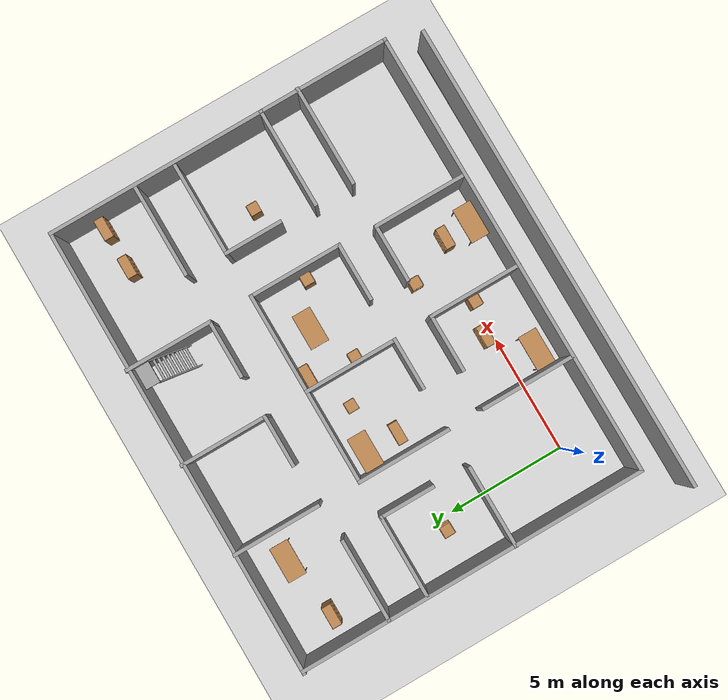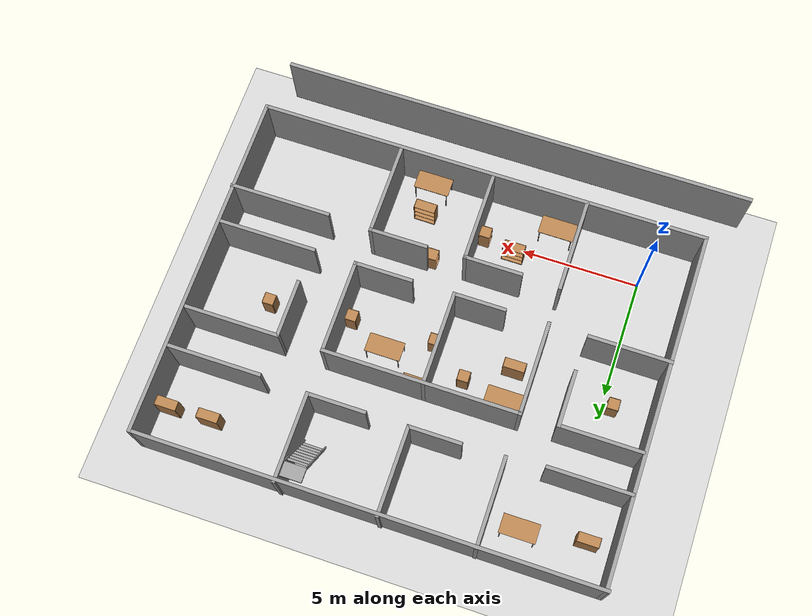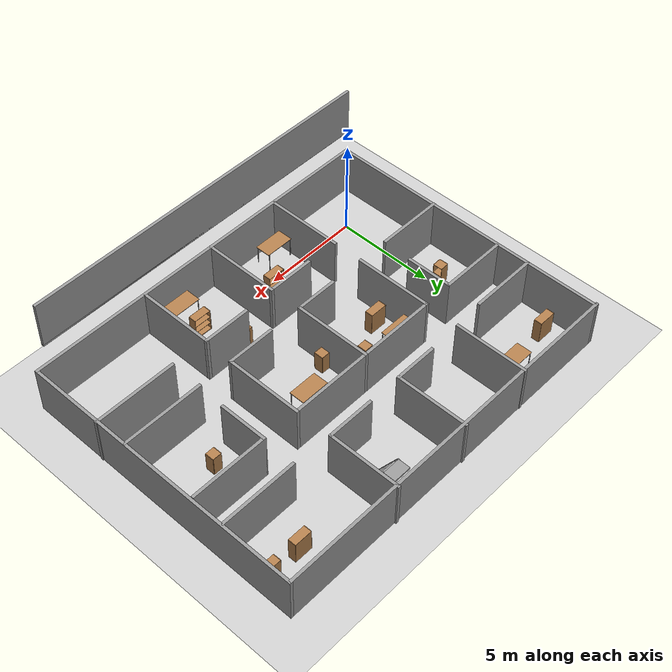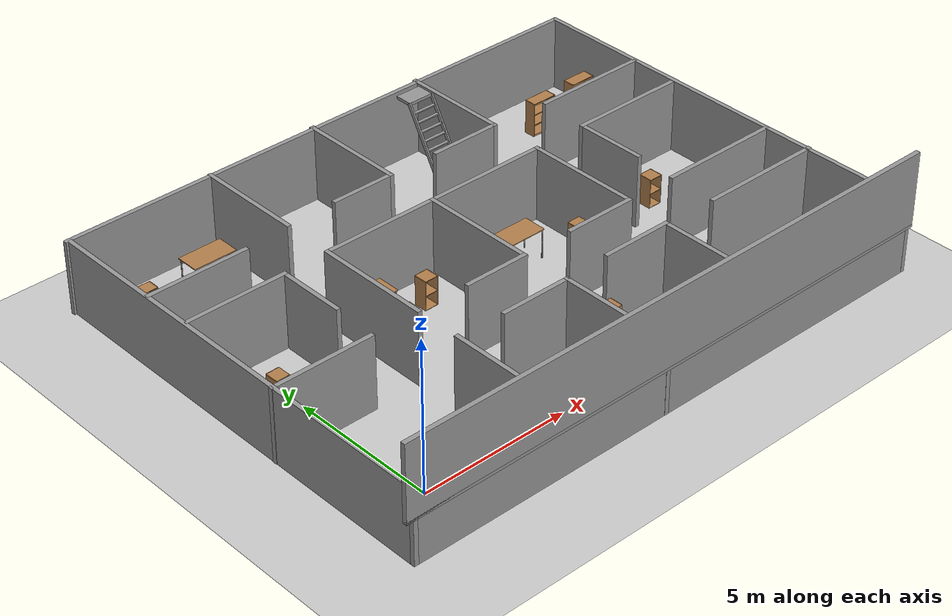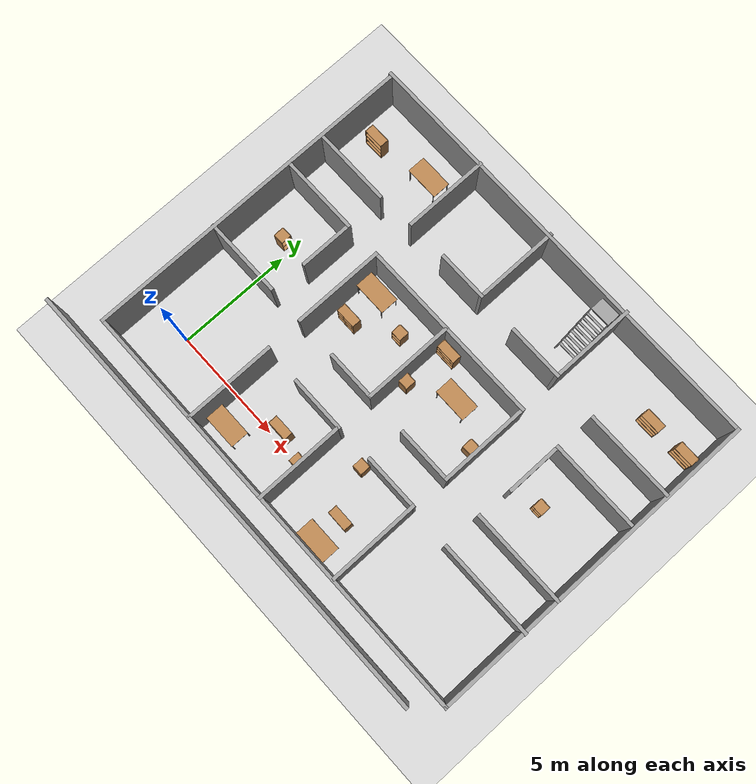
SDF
<sdf version="1.7">
 <world name="default">
  <light name="sun" type="directional">
   <pose>0 0 10 0 -0 0</pose>
   <diffuse>0.8 0.8 0.8 1</diffuse>
   <specular>0.2 0.2 0.2 1</specular>
   <attenuation>
    <range>1000</range>
    <constant>0.9</constant>
    <linear>0.01</linear>
    <quadratic>0.001</quadratic>
   </attenuation>
   <direction>-0.5 0.1 -0.9</direction>
   <spot><inner_angle>0</inner_angle><outer_angle>0</outer_angle><falloff>0</falloff></spot>
  </light>
  <model name="ground_plane">
   <static>1</static>
   <link name="link">
    <collision name="collision">
     <geometry><plane><normal>0 0 1</normal><size>100 100</size></plane></geometry>
     <surface><friction><ode><mu>100</mu><mu2>50</mu2></ode></friction></surface>
    </collision>
    <visual name="visual">
     <cast_shadows>0</cast_shadows>
     <geometry><plane><normal>0 0 1</normal><size>100 100</size></plane></geometry>
     <material>
      <script><uri>file://media/materials/scripts/gazebo.material</uri><name>Gazebo/Grey</name></script>
     </material>
    </visual>
   </link>
  </model>
  <gravity>0 0 -9.8</gravity>
  <magnetic_field>6e-06 2.3e-05 -4.2e-05</magnetic_field>
  <atmosphere type="adiabatic"/>
  <physics type="ode">
   <max_step_size>0.001</max_step_size>
   <real_time_factor>1</real_time_factor>
   <real_time_update_rate>1000</real_time_update_rate>
  </physics>
  <scene><ambient>0.4 0.4 0.4 1</ambient><background>0.7 0.7 0.7 1</background><shadows>1</shadows></scene>
  <spherical_coordinates>
   <surface_model>EARTH_WGS84</surface_model>
   <latitude_deg>0</latitude_deg>
   <longitude_deg>0</longitude_deg>
   <elevation>0</elevation>
   <heading_deg>0</heading_deg>
  </spherical_coordinates>
  <model name="indoors_2">
   <pose>7.49118 5.50535 0 0 -0 0</pose>
   <link name="Floor_0">
    <collision name="Floor_0_Collision">
     <geometry><box><size>19 0.15 0.1</size></box></geometry>
     <pose>0 0 0.05 0 -0 0</pose>
    </collision>
    <visual name="Floor_0_Visual">
     <pose>0 0 0.05 0 -0 0</pose>
     <geometry><box><size>19 0.15 0.1</size></box></geometry>
     <material>
      <script><uri>file://media/materials/scripts/gazebo.material</uri><name>Gazebo/Grey</name></script>
      <ambient>1 1 1 1</ambient>
     </material>
     <meta><layer>1</layer></meta>
    </visual>
    <pose>-1.02608 -8.28602 2.5 0 -0 0</pose>
   </link>
   <link name="Wall_0">
    <collision name="Wall_0_Collision">
     <geometry><box><size>19.15 0.15 2.5</size></box></geometry>
     <pose>0 0 1.25 0 -0 0</pose>
    </collision>
    <visual name="Wall_0_Visual">
     <pose>0 0 1.25 0 -0 0</pose>
     <geometry><box><size>19.15 0.15 2.5</size></box></geometry>
     <material>
      <script><uri>file://media/materials/scripts/gazebo.material</uri><name>Gazebo/Grey</name></script>
      <ambient>1 1 1 1</ambient>
     </material>
     <meta><layer>0</layer></meta>
    </visual>
    <pose>0.018922 -7.38602 0 0 -0 0</pose>
   </link>
   <link name="Wall_10">
    <collision name="Wall_10_Collision">
     <geometry><box><size>4 0.15 2.5</size></box></geometry>
     <pose>0 0 1.25 0 -0 0</pose>
    </collision>
    <visual name="Wall_10_Visual">
     <pose>0 0 1.25 0 -0 0</pose>
     <geometry><box><size>4 0.15 2.5</size></box></geometry>
     <material>
      <script><uri>file://media/materials/scripts/gazebo.material</uri><name>Gazebo/Grey</name></script>
      <ambient>1 1 1 1</ambient>
     </material>
     <meta><layer>0</layer></meta>
    </visual>
    <pose>-4.48108 -5.40902 0 0 -0 1.5708</pose>
   </link>
   <link name="Wall_12">
    <collision name="Wall_12_Collision">
     <geometry><box><size>4 0.15 2.5</size></box></geometry>
     <pose>0 0 1.25 0 -0 0</pose>
    </collision>
    <visual name="Wall_12_Visual">
     <pose>0 0 1.25 0 -0 0</pose>
     <geometry><box><size>4 0.15 2.5</size></box></geometry>
     <material>
      <script><uri>file://media/materials/scripts/gazebo.material</uri><name>Gazebo/Grey</name></script>
      <ambient>1 1 1 1</ambient>
     </material>
     <meta><layer>0</layer></meta>
    </visual>
    <pose>-0.481078 -5.46502 0 0 -0 1.5708</pose>
   </link>
   <link name="Wall_14">
    <collision name="Wall_14_Collision">
     <geometry><box><size>4 0.15 2.5</size></box></geometry>
     <pose>0 0 1.25 0 -0 0</pose>
    </collision>
    <visual name="Wall_14_Visual">
     <pose>0 0 1.25 0 -0 0</pose>
     <geometry><box><size>4 0.15 2.5</size></box></geometry>
     <material>
      <script><uri>file://media/materials/scripts/gazebo.material</uri><name>Gazebo/Grey</name></script>
      <ambient>1 1 1 1</ambient>
     </material>
     <meta><layer>0</layer></meta>
    </visual>
    <pose>3.51892 -5.39402 0 0 -0 1.5708</pose>
   </link>
   <link name="Wall_16">
    <collision name="Wall_16_Collision">
     <geometry><box><size>4.3 0.15 2.5</size></box></geometry>
     <pose>0 0 1.25 0 -0 0</pose>
    </collision>
    <visual name="Wall_16_Visual">
     <pose>0 0 1.25 0 -0 0</pose>
     <geometry><box><size>4.3 0.15 2.5</size></box></geometry>
     <material>
      <script><uri>file://media/materials/scripts/gazebo.material</uri><name>Gazebo/Grey</name></script>
      <ambient>1 1 1 1</ambient>
     </material>
     <meta><layer>0</layer></meta>
    </visual>
    <pose>7.47943 -3.5532 0 0 -0 3.14159</pose>
   </link>
   <link name="Wall_18">
    <collision name="Wall_18_Collision">
     <geometry><box><size>2.5 0.15 2.5</size></box></geometry>
     <pose>0 0 1.25 0 -0 0</pose>
    </collision>
    <visual name="Wall_18_Visual">
     <pose>0 0 1.25 0 -0 0</pose>
     <geometry><box><size>2.5 0.15 2.5</size></box></geometry>
     <material>
      <script><uri>file://media/materials/scripts/gazebo.material</uri><name>Gazebo/Grey</name></script>
      <ambient>1 1 1 1</ambient>
     </material>
     <meta><layer>0</layer></meta>
    </visual>
    <pose>-1.65608 -3.54002 0 0 -0 3.14159</pose>
   </link>
   <link name="Wall_2">
    <collision name="Wall_2_Collision">
     <geometry><box><size>19 0.15 2.5</size></box></geometry>
     <pose>0 0 1.25 0 -0 0</pose>
    </collision>
    <visual name="Wall_2_Visual">
     <pose>0 0 1.25 0 -0 0</pose>
     <geometry><box><size>19 0.15 2.5</size></box></geometry>
     <material>
      <script><uri>file://media/materials/scripts/gazebo.material</uri><name>Gazebo/Grey</name></script>
      <ambient>1 1 1 1</ambient>
     </material>
     <meta><layer>1</layer></meta>
    </visual>
    <pose>-1.02608 -8.28602 2.5 0 -0 0</pose>
   </link>
   <link name="Wall_20">
    <collision name="Wall_20_Collision">
     <geometry><box><size>2.5 0.15 2.5</size></box></geometry>
     <pose>0 0 1.25 0 -0 0</pose>
    </collision>
    <visual name="Wall_20_Visual">
     <pose>0 0 1.25 0 -0 0</pose>
     <geometry><box><size>2.5 0.15 2.5</size></box></geometry>
     <material>
      <script><uri>file://media/materials/scripts/gazebo.material</uri><name>Gazebo/Grey</name></script>
      <ambient>1 1 1 1</ambient>
     </material>
     <meta><layer>0</layer></meta>
    </visual>
    <pose>2.34392 -3.46902 0 0 -0 3.14159</pose>
   </link>
   <link name="Wall_22">
    <collision name="Wall_22_Collision">
     <geometry><box><size>3.5 0.15 2.5</size></box></geometry>
     <pose>0 0 1.25 0 -0 0</pose>
    </collision>
    <visual name="Wall_22_Visual">
     <pose>0 0 1.25 0 -0 0</pose>
     <geometry><box><size>3.5 0.15 2.5</size></box></geometry>
     <material>
      <script><uri>file://media/materials/scripts/gazebo.material</uri><name>Gazebo/Grey</name></script>
      <ambient>1 1 1 1</ambient>
     </material>
     <meta><layer>0</layer></meta>
    </visual>
    <pose>-7.82308 -1.88602 0 0 -0 0</pose>
   </link>
   <link name="Wall_24">
    <collision name="Wall_24_Collision">
     <geometry><box><size>3.5 0.15 2.5</size></box></geometry>
     <pose>0 0 1.25 0 -0 0</pose>
    </collision>
    <visual name="Wall_24_Visual">
     <pose>0 0 1.25 0 -0 0</pose>
     <geometry><box><size>3.5 0.15 2.5</size></box></geometry>
     <material>
      <script><uri>file://media/materials/scripts/gazebo.material</uri><name>Gazebo/Grey</name></script>
      <ambient>1 1 1 1</ambient>
     </material>
     <meta><layer>0</layer></meta>
    </visual>
    <pose>-7.71259 1.93002 0 0 -0 0</pose>
   </link>
   <link name="Wall_26">
    <collision name="Wall_26_Collision">
     <geometry><box><size>2.4 0.15 2.5</size></box></geometry>
     <pose>0 0 1.25 0 -0 0</pose>
    </collision>
    <visual name="Wall_26_Visual">
     <pose>0 0 1.25 0 -0 0</pose>
     <geometry><box><size>2.4 0.15 2.5</size></box></geometry>
     <material>
      <script><uri>file://media/materials/scripts/gazebo.material</uri><name>Gazebo/Grey</name></script>
      <ambient>1 1 1 1</ambient>
     </material>
     <meta><layer>0</layer></meta>
    </visual>
    <pose>-6.03759 0.805015 0 0 -0 -1.5708</pose>
   </link>
   <link name="Wall_28">
    <collision name="Wall_28_Collision">
     <geometry><box><size>3.5 0.15 2.5</size></box></geometry>
     <pose>0 0 1.25 0 -0 0</pose>
    </collision>
    <visual name="Wall_28_Visual">
     <pose>0 0 1.25 0 -0 0</pose>
     <geometry><box><size>3.5 0.15 2.5</size></box></geometry>
     <material>
      <script><uri>file://media/materials/scripts/gazebo.material</uri><name>Gazebo/Grey</name></script>
      <ambient>1 1 1 1</ambient>
     </material>
     <meta><layer>0</layer></meta>
    </visual>
    <pose>-7.76808 3.61398 0 0 -0 0</pose>
   </link>
   <link name="Wall_32">
    <collision name="Wall_32_Collision">
     <geometry><box><size>4 0.15 2.5</size></box></geometry>
     <pose>0 0 1.25 0 -0 0</pose>
    </collision>
    <visual name="Wall_32_Visual">
     <pose>0 0 1.25 0 -0 0</pose>
     <geometry><box><size>4 0.15 2.5</size></box></geometry>
     <material>
      <script><uri>file://media/materials/scripts/gazebo.material</uri><name>Gazebo/Grey</name></script>
      <ambient>1 1 1 1</ambient>
     </material>
     <meta><layer>0</layer></meta>
    </visual>
    <pose>-4.49048 0.026184 0 0 -0 1.5708</pose>
   </link>
   <link name="Wall_34">
    <collision name="Wall_34_Collision">
     <geometry><box><size>8.25 0.15 2.5</size></box></geometry>
     <pose>0 0 1.25 0 -0 0</pose>
    </collision>
    <visual name="Wall_34_Visual">
     <pose>0 0 1.25 0 -0 0</pose>
     <geometry><box><size>8.25 0.15 2.5</size></box></geometry>
     <material>
      <script><uri>file://media/materials/scripts/gazebo.material</uri><name>Gazebo/Grey</name></script>
      <ambient>1 1 1 1</ambient>
     </material>
     <meta><layer>0</layer></meta>
    </visual>
    <pose>-0.440485 1.95118 0 0 -0 0</pose>
   </link>
   <link name="Wall_35">
    <collision name="Wall_35_Collision">
     <geometry><box><size>4 0.15 2.5</size></box></geometry>
     <pose>0 0 1.25 0 -0 0</pose>
    </collision>
    <visual name="Wall_35_Visual">
     <pose>0 0 1.25 0 -0 0</pose>
     <geometry><box><size>4 0.15 2.5</size></box></geometry>
     <material>
      <script><uri>file://media/materials/scripts/gazebo.material</uri><name>Gazebo/Grey</name></script>
      <ambient>1 1 1 1</ambient>
     </material>
     <meta><layer>0</layer></meta>
    </visual>
    <pose>3.60952 0.026184 0 0 -0 -1.5708</pose>
   </link>
   <link name="Wall_37">
    <collision name="Wall_37_Collision">
     <geometry><box><size>2.5 0.15 2.5</size></box></geometry>
     <pose>0 0 1.25 0 -0 0</pose>
    </collision>
    <visual name="Wall_37_Visual">
     <pose>0 0 1.25 0 -0 0</pose>
     <geometry><box><size>2.5 0.15 2.5</size></box></geometry>
     <material>
      <script><uri>file://media/materials/scripts/gazebo.material</uri><name>Gazebo/Grey</name></script>
      <ambient>1 1 1 1</ambient>
     </material>
     <meta><layer>0</layer></meta>
    </visual>
    <pose>2.43452 -1.89882 0 0 -0 3.14159</pose>
   </link>
   <link name="Wall_39">
    <collision name="Wall_39_Collision">
     <geometry><box><size>4 0.15 2.5</size></box></geometry>
     <pose>0 0 1.25 0 -0 0</pose>
    </collision>
    <visual name="Wall_39_Visual">
     <pose>0 0 1.25 0 -0 0</pose>
     <geometry><box><size>4 0.15 2.5</size></box></geometry>
     <material>
      <script><uri>file://media/materials/scripts/gazebo.material</uri><name>Gazebo/Grey</name></script>
      <ambient>1 1 1 1</ambient>
     </material>
     <meta><layer>0</layer></meta>
    </visual>
    <pose>-0.557426 0.026184 0 0 -0 1.5708</pose>
   </link>
   <link name="Wall_4">
    <collision name="Wall_4_Collision">
     <geometry><box><size>14.8671 0.15 2.5</size></box></geometry>
     <pose>0 0 1.25 0 -0 0</pose>
    </collision>
    <visual name="Wall_4_Visual">
     <pose>0 0 1.25 0 -0 0</pose>
     <geometry><box><size>14.8671 0.15 2.5</size></box></geometry>
     <material>
      <script><uri>file://media/materials/scripts/gazebo.material</uri><name>Gazebo/Grey</name></script>
      <ambient>1 1 1 1</ambient>
     </material>
     <meta><layer>0</layer></meta>
    </visual>
    <pose>-9.48108 -0.027809 0 0 -0 1.5708</pose>
   </link>
   <link name="Wall_42">
    <collision name="Wall_42_Collision">
     <geometry><box><size>2.25 0.15 2.5</size></box></geometry>
     <pose>0 0 1.25 0 -0 0</pose>
    </collision>
    <visual name="Wall_42_Visual">
     <pose>0 0 1.25 0 -0 0</pose>
     <geometry><box><size>2.25 0.15 2.5</size></box></geometry>
     <material>
      <script><uri>file://media/materials/scripts/gazebo.material</uri><name>Gazebo/Grey</name></script>
      <ambient>1 1 1 1</ambient>
     </material>
     <meta><layer>0</layer></meta>
    </visual>
    <pose>-1.60743 -1.89882 0 0 -0 3.14159</pose>
   </link>
   <link name="Wall_44">
    <collision name="Wall_44_Collision">
     <geometry><box><size>4.25 0.15 2.5</size></box></geometry>
     <pose>0 0 1.25 0 -0 0</pose>
    </collision>
    <visual name="Wall_44_Visual">
     <pose>0 0 1.25 0 -0 0</pose>
     <geometry><box><size>4.25 0.15 2.5</size></box></geometry>
     <material>
      <script><uri>file://media/materials/scripts/gazebo.material</uri><name>Gazebo/Grey</name></script>
      <ambient>1 1 1 1</ambient>
     </material>
     <meta><layer>0</layer></meta>
    </visual>
    <pose>7.45621 -1.91179 0 0 -0 0</pose>
   </link>
   <link name="Wall_46">
    <collision name="Wall_46_Collision">
     <geometry><box><size>4 0.15 2.5</size></box></geometry>
     <pose>0 0 1.25 0 -0 0</pose>
    </collision>
    <visual name="Wall_46_Visual">
     <pose>0 0 1.25 0 -0 0</pose>
     <geometry><box><size>4 0.15 2.5</size></box></geometry>
     <material>
      <script><uri>file://media/materials/scripts/gazebo.material</uri><name>Gazebo/Grey</name></script>
      <ambient>1 1 1 1</ambient>
     </material>
     <meta><layer>0</layer></meta>
    </visual>
    <pose>7.42753 1.94115 0 0 -0 0</pose>
   </link>
   <link name="Wall_48">
    <collision name="Wall_48_Collision">
     <geometry><box><size>2.5 0.15 2.5</size></box></geometry>
     <pose>0 0 1.25 0 -0 0</pose>
    </collision>
    <visual name="Wall_48_Visual">
     <pose>0 0 1.25 0 -0 0</pose>
     <geometry><box><size>2.5 0.15 2.5</size></box></geometry>
     <material>
      <script><uri>file://media/materials/scripts/gazebo.material</uri><name>Gazebo/Grey</name></script>
      <ambient>1 1 1 1</ambient>
     </material>
     <meta><layer>0</layer></meta>
    </visual>
    <pose>5.50253 0.766149 0 0 -0 -1.5708</pose>
   </link>
   <link name="Wall_50">
    <collision name="Wall_50_Collision">
     <geometry><box><size>3.75 0.15 2.5</size></box></geometry>
     <pose>0 0 1.25 0 -0 0</pose>
    </collision>
    <visual name="Wall_50_Visual">
     <pose>0 0 1.25 0 -0 0</pose>
     <geometry><box><size>3.75 0.15 2.5</size></box></geometry>
     <material>
      <script><uri>file://media/materials/scripts/gazebo.material</uri><name>Gazebo/Grey</name></script>
      <ambient>1 1 1 1</ambient>
     </material>
     <meta><layer>0</layer></meta>
    </visual>
    <pose>-4.46932 5.55322 0 0 -0 -1.5708</pose>
   </link>
   <link name="Wall_52">
    <collision name="Wall_52_Collision">
     <geometry><box><size>3.75 0.15 2.5</size></box></geometry>
     <pose>0 0 1.25 0 -0 0</pose>
    </collision>
    <visual name="Wall_52_Visual">
     <pose>0 0 1.25 0 -0 0</pose>
     <geometry><box><size>3.75 0.15 2.5</size></box></geometry>
     <material>
      <script><uri>file://media/materials/scripts/gazebo.material</uri><name>Gazebo/Grey</name></script>
      <ambient>1 1 1 1</ambient>
     </material>
     <meta><layer>0</layer></meta>
    </visual>
    <pose>-0.580388 5.59002 0 0 -0 1.5708</pose>
   </link>
   <link name="Wall_54">
    <collision name="Wall_54_Collision">
     <geometry><box><size>3.75 0.15 2.5</size></box></geometry>
     <pose>0 0 1.25 0 -0 0</pose>
    </collision>
    <visual name="Wall_54_Visual">
     <pose>0 0 1.25 0 -0 0</pose>
     <geometry><box><size>3.75 0.15 2.5</size></box></geometry>
     <material>
      <script><uri>file://media/materials/scripts/gazebo.material</uri><name>Gazebo/Grey</name></script>
      <ambient>1 1 1 1</ambient>
     </material>
     <meta><layer>0</layer></meta>
    </visual>
    <pose>3.55972 5.59002 0 0 -0 1.5708</pose>
   </link>
   <link name="Wall_56">
    <collision name="Wall_56_Collision">
     <geometry><box><size>2.5 0.15 2.5</size></box></geometry>
     <pose>0 0 1.25 0 -0 0</pose>
    </collision>
    <visual name="Wall_56_Visual">
     <pose>0 0 1.25 0 -0 0</pose>
     <geometry><box><size>2.5 0.15 2.5</size></box></geometry>
     <material>
      <script><uri>file://media/materials/scripts/gazebo.material</uri><name>Gazebo/Grey</name></script>
      <ambient>1 1 1 1</ambient>
     </material>
     <meta><layer>0</layer></meta>
    </visual>
    <pose>2.38472 3.79002 0 0 -0 0</pose>
   </link>
   <link name="Wall_58">
    <collision name="Wall_58_Collision">
     <geometry><box><size>2.25 0.15 2.5</size></box></geometry>
     <pose>0 0 1.25 0 -0 0</pose>
    </collision>
    <visual name="Wall_58_Visual">
     <pose>0 0 1.25 0 -0 0</pose>
     <geometry><box><size>2.25 0.15 2.5</size></box></geometry>
     <material>
      <script><uri>file://media/materials/scripts/gazebo.material</uri><name>Gazebo/Grey</name></script>
      <ambient>1 1 1 1</ambient>
     </material>
     <meta><layer>0</layer></meta>
    </visual>
    <pose>-1.63039 3.79002 0 0 -0 0</pose>
   </link>
   <link name="Wall_6">
    <collision name="Wall_6_Collision">
     <geometry><box><size>14.8402 0.15 2.5</size></box></geometry>
     <pose>0 0 1.25 0 -0 0</pose>
    </collision>
    <visual name="Wall_6_Visual">
     <pose>0 0 1.25 0 -0 0</pose>
     <geometry><box><size>14.8402 0.15 2.5</size></box></geometry>
     <material>
      <script><uri>file://media/materials/scripts/gazebo.material</uri><name>Gazebo/Grey</name></script>
      <ambient>1 1 1 1</ambient>
     </material>
     <meta><layer>0</layer></meta>
    </visual>
    <pose>9.51892 -0.041274 0 0 -0 1.5708</pose>
   </link>
   <link name="Wall_60">
    <collision name="Wall_60_Collision">
     <geometry><box><size>4 0.15 2.5</size></box></geometry>
     <pose>0 0 1.25 0 -0 0</pose>
    </collision>
    <visual name="Wall_60_Visual">
     <pose>0 0 1.25 0 -0 0</pose>
     <geometry><box><size>4 0.15 2.5</size></box></geometry>
     <material>
      <script><uri>file://media/materials/scripts/gazebo.material</uri><name>Gazebo/Grey</name></script>
      <ambient>1 1 1 1</ambient>
     </material>
     <meta><layer>0</layer></meta>
    </visual>
    <pose>7.52292 3.66263 0 0 -0 0</pose>
   </link>
   <link name="Wall_8">
    <collision name="Wall_8_Collision">
     <geometry><box><size>19.15 0.15 2.5</size></box></geometry>
     <pose>0 0 1.25 0 -0 0</pose>
    </collision>
    <visual name="Wall_8_Visual">
     <pose>0 0 1.25 0 -0 0</pose>
     <geometry><box><size>19.15 0.15 2.5</size></box></geometry>
     <material>
      <script><uri>file://media/materials/scripts/gazebo.material</uri><name>Gazebo/Grey</name></script>
      <ambient>1 1 1 1</ambient>
     </material>
     <meta><layer>0</layer></meta>
    </visual>
    <pose>-0.054326 7.31693 0 0 -0 -0.001417</pose>
   </link>
   <static>1</static>
  </model>
  <model name="table">
   <static>1</static>
   <link name="link">
    <collision name="surface">
     <pose>0 0 1 0 -0 0</pose>
     <geometry><box><size>1.5 0.8 0.03</size></box></geometry>
     <surface><friction><ode><mu>0.6</mu><mu2>0.6</mu2></ode></friction></surface>
    </collision>
    <visual name="visual1">
     <pose>0 0 1 0 -0 0</pose>
     <geometry><box><size>1.5 0.8 0.03</size></box></geometry>
     <material>
      <script><uri>file://media/materials/scripts/gazebo.material</uri><name>Gazebo/Wood</name></script>
     </material>
    </visual>
    <collision name="front_left_leg">
     <pose>0.68 0.38 0.5 0 -0 0</pose>
     <geometry><cylinder><radius>0.02</radius><length>1</length></cylinder></geometry>
    </collision>
    <visual name="front_left_leg">
     <pose>0.68 0.38 0.5 0 -0 0</pose>
     <geometry><cylinder><radius>0.02</radius><length>1</length></cylinder></geometry>
     <material>
      <script><uri>file://media/materials/scripts/gazebo.material</uri><name>Gazebo/Grey</name></script>
     </material>
    </visual>
    <collision name="front_right_leg">
     <pose>0.68 -0.38 0.5 0 -0 0</pose>
     <geometry><cylinder><radius>0.02</radius><length>1</length></cylinder></geometry>
    </collision>
    <visual name="front_right_leg">
     <pose>0.68 -0.38 0.5 0 -0 0</pose>
     <geometry><cylinder><radius>0.02</radius><length>1</length></cylinder></geometry>
     <material>
      <script><uri>file://media/materials/scripts/gazebo.material</uri><name>Gazebo/Grey</name></script>
     </material>
    </visual>
    <collision name="back_right_leg">
     <pose>-0.68 -0.38 0.5 0 -0 0</pose>
     <geometry><cylinder><radius>0.02</radius><length>1</length></cylinder></geometry>
    </collision>
    <visual name="back_right_leg">
     <pose>-0.68 -0.38 0.5 0 -0 0</pose>
     <geometry><cylinder><radius>0.02</radius><length>1</length></cylinder></geometry>
     <material>
      <script><uri>file://media/materials/scripts/gazebo.material</uri><name>Gazebo/Grey</name></script>
     </material>
    </visual>
    <collision name="back_left_leg">
     <pose>-0.68 0.38 0.5 0 -0 0</pose>
     <geometry><cylinder><radius>0.02</radius><length>1</length></cylinder></geometry>
    </collision>
    <visual name="back_left_leg">
     <pose>-0.68 0.38 0.5 0 -0 0</pose>
     <geometry><cylinder><radius>0.02</radius><length>1</length></cylinder></geometry>
     <material>
      <script><uri>file://media/materials/scripts/gazebo.material</uri><name>Gazebo/Grey</name></script>
     </material>
    </visual>
   </link>
   <pose>9.03826 6.14095 0 0 -0 0</pose>
  </model>
  <model name="bookshelf">
   <static>1</static>
   <link name="link">
    <inertial><mass>1</mass></inertial>
    <collision name="back">
     <pose>0 0.005 0.6 0 -0 0</pose>
     <geometry><box><size>0.9 0.01 1.2</size></box></geometry>
    </collision>
    <visual name="visual1">
     <pose>0 0.005 0.6 0 -0 0</pose>
     <geometry><box><size>0.9 0.01 1.2</size></box></geometry>
     <material>
      <script><uri>file://media/materials/scripts/gazebo.material</uri><name>Gazebo/Wood</name></script>
     </material>
    </visual>
    <collision name="left_side">
     <pose>0.45 -0.195 0.6 0 -0 0</pose>
     <geometry><box><size>0.02 0.4 1.2</size></box></geometry>
    </collision>
    <visual name="visual2">
     <pose>0.45 -0.195 0.6 0 -0 0</pose>
     <geometry><box><size>0.02 0.4 1.2</size></box></geometry>
     <material>
      <script><uri>file://media/materials/scripts/gazebo.material</uri><name>Gazebo/Wood</name></script>
     </material>
    </visual>
    <collision name="right_side">
     <pose>-0.45 -0.195 0.6 0 -0 0</pose>
     <geometry><box><size>0.02 0.4 1.2</size></box></geometry>
    </collision>
    <visual name="visual3">
     <pose>-0.45 -0.195 0.6 0 -0 0</pose>
     <geometry><box><size>0.02 0.4 1.2</size></box></geometry>
     <material>
      <script><uri>file://media/materials/scripts/gazebo.material</uri><name>Gazebo/Wood</name></script>
     </material>
    </visual>
    <collision name="bottom">
     <pose>0 -0.195 0.03 0 -0 0</pose>
     <geometry><box><size>0.88 0.4 0.06</size></box></geometry>
    </collision>
    <visual name="visual4">
     <pose>0 -0.195 0.03 0 -0 0</pose>
     <geometry><box><size>0.88 0.4 0.06</size></box></geometry>
     <material>
      <script><uri>file://media/materials/scripts/gazebo.material</uri><name>Gazebo/Wood</name></script>
     </material>
    </visual>
    <collision name="top">
     <pose>0 -0.195 1.19 0 -0 0</pose>
     <geometry><box><size>0.88 0.4 0.02</size></box></geometry>
    </collision>
    <visual name="visual5">
     <pose>0 -0.195 1.19 0 -0 0</pose>
     <geometry><box><size>0.88 0.4 0.02</size></box></geometry>
     <material>
      <script><uri>file://media/materials/scripts/gazebo.material</uri><name>Gazebo/Wood</name></script>
     </material>
    </visual>
    <collision name="low_shelf">
     <pose>0 -0.195 0.43 0 -0 0</pose>
     <geometry><box><size>0.88 0.4 0.02</size></box></geometry>
    </collision>
    <visual name="visual6">
     <pose>0 -0.195 0.43 0 -0 0</pose>
     <geometry><box><size>0.88 0.4 0.02</size></box></geometry>
     <material>
      <script><uri>file://media/materials/scripts/gazebo.material</uri><name>Gazebo/Wood</name></script>
     </material>
    </visual>
    <collision name="high_shelf">
     <pose>0 -0.195 0.8 0 -0 0</pose>
     <geometry><box><size>0.88 0.4 0.02</size></box></geometry>
    </collision>
    <visual name="visual7">
     <pose>0 -0.195 0.8 0 -0 0</pose>
     <geometry><box><size>0.88 0.4 0.02</size></box></geometry>
     <material>
      <script><uri>file://media/materials/scripts/gazebo.material</uri><name>Gazebo/Wood</name></script>
     </material>
    </visual>
   </link>
   <pose>7.47775 7.35684 0 0 -0 0</pose>
  </model>
  <model name="cabinet">
   <static>1</static>
   <link name="cabinet_bottom_plate">
    <inertial>
     <pose>0 0 -1 0 -0 0</pose>
     <inertia><ixx>2.05</ixx><ixy>0</ixy><ixz>0</ixz><iyy>2.05</iyy><iyz>0</iyz><izz>2.05</izz></inertia>
     <mass>25</mass>
    </inertial>
    <collision name="cabinet_bottom_plate_geom">
     <pose>0 0 0.01 0 -0 0</pose>
     <geometry><box><size>0.45 0.45 0.02</size></box></geometry>
    </collision>
    <visual name="cabinet_bottom_plate_geom_visual">
     <pose>0 0 0.01 0 -0 0</pose>
     <geometry><box><size>0.45 0.45 0.02</size></box></geometry>
     <material>
      <script><uri>file://media/materials/scripts/gazebo.material</uri><name>Gazebo/Wood</name></script>
     </material>
    </visual>
    <collision name="cabinet_bottom_plate_geom_cabinet_back_plate">
     <pose>0.235 0 0.51 0 -0 0</pose>
     <geometry><box><size>0.02 0.45 1.02</size></box></geometry>
    </collision>
    <visual name="cabinet_bottom_plate_geom_cabinet_back_plate_visual">
     <pose>0.235 0 0.51 0 -0 0</pose>
     <geometry><box><size>0.02 0.45 1.02</size></box></geometry>
     <material>
      <script><uri>file://media/materials/scripts/gazebo.material</uri><name>Gazebo/Wood</name></script>
     </material>
    </visual>
    <collision name="cabinet_bottom_plate_geom_cabinet_left_plate">
     <pose>0 0.235 0.51 0 -0 0</pose>
     <geometry><box><size>0.45 0.02 1.02</size></box></geometry>
    </collision>
    <visual name="cabinet_bottom_plate_geom_cabinet_left_plate_visual">
     <pose>0 0.235 0.51 0 -0 0</pose>
     <geometry><box><size>0.45 0.02 1.02</size></box></geometry>
     <material>
      <script><uri>file://media/materials/scripts/gazebo.material</uri><name>Gazebo/Wood</name></script>
     </material>
    </visual>
    <collision name="cabinet_bottom_plate_geom_cabinet_middle_plate">
     <pose>0 0 0.51 0 -0 0</pose>
     <geometry><box><size>0.45 0.45 0.02</size></box></geometry>
    </collision>
    <visual name="cabinet_bottom_plate_geom_cabinet_middle_plate_visual">
     <pose>0 0 0.51 0 -0 0</pose>
     <geometry><box><size>0.45 0.45 0.02</size></box></geometry>
     <material>
      <script><uri>file://media/materials/scripts/gazebo.material</uri><name>Gazebo/Wood</name></script>
     </material>
    </visual>
    <collision name="cabinet_bottom_plate_geom_cabinet_right_plate">
     <pose>0 -0.235 0.51 0 -0 0</pose>
     <geometry><box><size>0.45 0.02 1.02</size></box></geometry>
    </collision>
    <visual name="cabinet_bottom_plate_geom_cabinet_right_plate_visual">
     <pose>0 -0.235 0.51 0 -0 0</pose>
     <geometry><box><size>0.45 0.02 1.02</size></box></geometry>
     <material>
      <script><uri>file://media/materials/scripts/gazebo.material</uri><name>Gazebo/Wood</name></script>
     </material>
    </visual>
    <collision name="cabinet_bottom_plate_geom_cabinet_top_plate">
     <pose>0 0 1.01 0 -0 0</pose>
     <geometry><box><size>0.45 0.45 0.02</size></box></geometry>
    </collision>
    <visual name="cabinet_bottom_plate_geom_cabinet_top_plate_visual">
     <pose>0 0 1.01 0 -0 0</pose>
     <geometry><box><size>0.45 0.45 0.02</size></box></geometry>
     <material>
      <script><uri>file://media/materials/scripts/gazebo.material</uri><name>Gazebo/Wood</name></script>
     </material>
    </visual>
   </link>
   <pose>10.7673 5.28422 0 0 0 -3.14159</pose>
  </model>
  <model name="cabinet_0">
   <static>1</static>
   <link name="cabinet_bottom_plate">
    <inertial>
     <pose>0 0 -1 0 -0 0</pose>
     <inertia><ixx>2.05</ixx><ixy>0</ixy><ixz>0</ixz><iyy>2.05</iyy><iyz>0</iyz><izz>2.05</izz></inertia>
     <mass>25</mass>
    </inertial>
    <collision name="cabinet_bottom_plate_geom">
     <pose>0 0 0.01 0 -0 0</pose>
     <geometry><box><size>0.45 0.45 0.02</size></box></geometry>
    </collision>
    <visual name="cabinet_bottom_plate_geom_visual">
     <pose>0 0 0.01 0 -0 0</pose>
     <geometry><box><size>0.45 0.45 0.02</size></box></geometry>
     <material>
      <script><uri>file://media/materials/scripts/gazebo.material</uri><name>Gazebo/Wood</name></script>
     </material>
    </visual>
    <collision name="cabinet_bottom_plate_geom_cabinet_back_plate">
     <pose>0.235 0 0.51 0 -0 0</pose>
     <geometry><box><size>0.02 0.45 1.02</size></box></geometry>
    </collision>
    <visual name="cabinet_bottom_plate_geom_cabinet_back_plate_visual">
     <pose>0.235 0 0.51 0 -0 0</pose>
     <geometry><box><size>0.02 0.45 1.02</size></box></geometry>
     <material>
      <script><uri>file://media/materials/scripts/gazebo.material</uri><name>Gazebo/Wood</name></script>
     </material>
    </visual>
    <collision name="cabinet_bottom_plate_geom_cabinet_left_plate">
     <pose>0 0.235 0.51 0 -0 0</pose>
     <geometry><box><size>0.45 0.02 1.02</size></box></geometry>
    </collision>
    <visual name="cabinet_bottom_plate_geom_cabinet_left_plate_visual">
     <pose>0 0.235 0.51 0 -0 0</pose>
     <geometry><box><size>0.45 0.02 1.02</size></box></geometry>
     <material>
      <script><uri>file://media/materials/scripts/gazebo.material</uri><name>Gazebo/Wood</name></script>
     </material>
    </visual>
    <collision name="cabinet_bottom_plate_geom_cabinet_middle_plate">
     <pose>0 0 0.51 0 -0 0</pose>
     <geometry><box><size>0.45 0.45 0.02</size></box></geometry>
    </collision>
    <visual name="cabinet_bottom_plate_geom_cabinet_middle_plate_visual">
     <pose>0 0 0.51 0 -0 0</pose>
     <geometry><box><size>0.45 0.45 0.02</size></box></geometry>
     <material>
      <script><uri>file://media/materials/scripts/gazebo.material</uri><name>Gazebo/Wood</name></script>
     </material>
    </visual>
    <collision name="cabinet_bottom_plate_geom_cabinet_right_plate">
     <pose>0 -0.235 0.51 0 -0 0</pose>
     <geometry><box><size>0.45 0.02 1.02</size></box></geometry>
    </collision>
    <visual name="cabinet_bottom_plate_geom_cabinet_right_plate_visual">
     <pose>0 -0.235 0.51 0 -0 0</pose>
     <geometry><box><size>0.45 0.02 1.02</size></box></geometry>
     <material>
      <script><uri>file://media/materials/scripts/gazebo.material</uri><name>Gazebo/Wood</name></script>
     </material>
    </visual>
    <collision name="cabinet_bottom_plate_geom_cabinet_top_plate">
     <pose>0 0 1.01 0 -0 0</pose>
     <geometry><box><size>0.45 0.45 0.02</size></box></geometry>
    </collision>
    <visual name="cabinet_bottom_plate_geom_cabinet_top_plate_visual">
     <pose>0 0 1.01 0 -0 0</pose>
     <geometry><box><size>0.45 0.45 0.02</size></box></geometry>
     <material>
      <script><uri>file://media/materials/scripts/gazebo.material</uri><name>Gazebo/Wood</name></script>
     </material>
    </visual>
   </link>
   <pose>7.21592 5.20257 0 0 -0 0</pose>
  </model>
  <model name="table_0">
   <static>1</static>
   <link name="link">
    <collision name="surface">
     <pose>0 0 1 0 -0 0</pose>
     <geometry><box><size>1.5 0.8 0.03</size></box></geometry>
     <surface><friction><ode><mu>0.6</mu><mu2>0.6</mu2></ode></friction></surface>
    </collision>
    <visual name="visual1">
     <pose>0 0 1 0 -0 0</pose>
     <geometry><box><size>1.5 0.8 0.03</size></box></geometry>
     <material>
      <script><uri>file://media/materials/scripts/gazebo.material</uri><name>Gazebo/Wood</name></script>
     </material>
    </visual>
    <collision name="front_left_leg">
     <pose>0.68 0.38 0.5 0 -0 0</pose>
     <geometry><cylinder><radius>0.02</radius><length>1</length></cylinder></geometry>
    </collision>
    <visual name="front_left_leg">
     <pose>0.68 0.38 0.5 0 -0 0</pose>
     <geometry><cylinder><radius>0.02</radius><length>1</length></cylinder></geometry>
     <material>
      <script><uri>file://media/materials/scripts/gazebo.material</uri><name>Gazebo/Grey</name></script>
     </material>
    </visual>
    <collision name="front_right_leg">
     <pose>0.68 -0.38 0.5 0 -0 0</pose>
     <geometry><cylinder><radius>0.02</radius><length>1</length></cylinder></geometry>
    </collision>
    <visual name="front_right_leg">
     <pose>0.68 -0.38 0.5 0 -0 0</pose>
     <geometry><cylinder><radius>0.02</radius><length>1</length></cylinder></geometry>
     <material>
      <script><uri>file://media/materials/scripts/gazebo.material</uri><name>Gazebo/Grey</name></script>
     </material>
    </visual>
    <collision name="back_right_leg">
     <pose>-0.68 -0.38 0.5 0 -0 0</pose>
     <geometry><cylinder><radius>0.02</radius><length>1</length></cylinder></geometry>
    </collision>
    <visual name="back_right_leg">
     <pose>-0.68 -0.38 0.5 0 -0 0</pose>
     <geometry><cylinder><radius>0.02</radius><length>1</length></cylinder></geometry>
     <material>
      <script><uri>file://media/materials/scripts/gazebo.material</uri><name>Gazebo/Grey</name></script>
     </material>
    </visual>
    <collision name="back_left_leg">
     <pose>-0.68 0.38 0.5 0 -0 0</pose>
     <geometry><cylinder><radius>0.02</radius><length>1</length></cylinder></geometry>
    </collision>
    <visual name="back_left_leg">
     <pose>-0.68 0.38 0.5 0 -0 0</pose>
     <geometry><cylinder><radius>0.02</radius><length>1</length></cylinder></geometry>
     <material>
      <script><uri>file://media/materials/scripts/gazebo.material</uri><name>Gazebo/Grey</name></script>
     </material>
    </visual>
   </link>
   <pose>9.46648 -1.38321 0 0 -0 0</pose>
  </model>
  <model name="cabinet_1">
   <static>1</static>
   <link name="cabinet_bottom_plate">
    <inertial>
     <pose>0 0 -1 0 -0 0</pose>
     <inertia><ixx>2.05</ixx><ixy>0</ixy><ixz>0</ixz><iyy>2.05</iyy><iyz>0</iyz><izz>2.05</izz></inertia>
     <mass>25</mass>
    </inertial>
    <collision name="cabinet_bottom_plate_geom">
     <pose>0 0 0.01 0 -0 0</pose>
     <geometry><box><size>0.45 0.45 0.02</size></box></geometry>
    </collision>
    <visual name="cabinet_bottom_plate_geom_visual">
     <pose>0 0 0.01 0 -0 0</pose>
     <geometry><box><size>0.45 0.45 0.02</size></box></geometry>
     <material>
      <script><uri>file://media/materials/scripts/gazebo.material</uri><name>Gazebo/Wood</name></script>
     </material>
    </visual>
    <collision name="cabinet_bottom_plate_geom_cabinet_back_plate">
     <pose>0.235 0 0.51 0 -0 0</pose>
     <geometry><box><size>0.02 0.45 1.02</size></box></geometry>
    </collision>
    <visual name="cabinet_bottom_plate_geom_cabinet_back_plate_visual">
     <pose>0.235 0 0.51 0 -0 0</pose>
     <geometry><box><size>0.02 0.45 1.02</size></box></geometry>
     <material>
      <script><uri>file://media/materials/scripts/gazebo.material</uri><name>Gazebo/Wood</name></script>
     </material>
    </visual>
    <collision name="cabinet_bottom_plate_geom_cabinet_left_plate">
     <pose>0 0.235 0.51 0 -0 0</pose>
     <geometry><box><size>0.45 0.02 1.02</size></box></geometry>
    </collision>
    <visual name="cabinet_bottom_plate_geom_cabinet_left_plate_visual">
     <pose>0 0.235 0.51 0 -0 0</pose>
     <geometry><box><size>0.45 0.02 1.02</size></box></geometry>
     <material>
      <script><uri>file://media/materials/scripts/gazebo.material</uri><name>Gazebo/Wood</name></script>
     </material>
    </visual>
    <collision name="cabinet_bottom_plate_geom_cabinet_middle_plate">
     <pose>0 0 0.51 0 -0 0</pose>
     <geometry><box><size>0.45 0.45 0.02</size></box></geometry>
    </collision>
    <visual name="cabinet_bottom_plate_geom_cabinet_middle_plate_visual">
     <pose>0 0 0.51 0 -0 0</pose>
     <geometry><box><size>0.45 0.45 0.02</size></box></geometry>
     <material>
      <script><uri>file://media/materials/scripts/gazebo.material</uri><name>Gazebo/Wood</name></script>
     </material>
    </visual>
    <collision name="cabinet_bottom_plate_geom_cabinet_right_plate">
     <pose>0 -0.235 0.51 0 -0 0</pose>
     <geometry><box><size>0.45 0.02 1.02</size></box></geometry>
    </collision>
    <visual name="cabinet_bottom_plate_geom_cabinet_right_plate_visual">
     <pose>0 -0.235 0.51 0 -0 0</pose>
     <geometry><box><size>0.45 0.02 1.02</size></box></geometry>
     <material>
      <script><uri>file://media/materials/scripts/gazebo.material</uri><name>Gazebo/Wood</name></script>
     </material>
    </visual>
    <collision name="cabinet_bottom_plate_geom_cabinet_top_plate">
     <pose>0 0 1.01 0 -0 0</pose>
     <geometry><box><size>0.45 0.45 0.02</size></box></geometry>
    </collision>
    <visual name="cabinet_bottom_plate_geom_cabinet_top_plate_visual">
     <pose>0 0 1.01 0 -0 0</pose>
     <geometry><box><size>0.45 0.45 0.02</size></box></geometry>
     <material>
      <script><uri>file://media/materials/scripts/gazebo.material</uri><name>Gazebo/Wood</name></script>
     </material>
    </visual>
   </link>
   <pose>8.49279 1.70409 0 0 -0 0</pose>
  </model>
  <model name="bookshelf_0">
   <static>1</static>
   <link name="link">
    <inertial><mass>1</mass></inertial>
    <collision name="back">
     <pose>0 0.005 0.6 0 -0 0</pose>
     <geometry><box><size>0.9 0.01 1.2</size></box></geometry>
    </collision>
    <visual name="visual1">
     <pose>0 0.005 0.6 0 -0 0</pose>
     <geometry><box><size>0.9 0.01 1.2</size></box></geometry>
     <material>
      <script><uri>file://media/materials/scripts/gazebo.material</uri><name>Gazebo/Wood</name></script>
     </material>
    </visual>
    <collision name="left_side">
     <pose>0.45 -0.195 0.6 0 -0 0</pose>
     <geometry><box><size>0.02 0.4 1.2</size></box></geometry>
    </collision>
    <visual name="visual2">
     <pose>0.45 -0.195 0.6 0 -0 0</pose>
     <geometry><box><size>0.02 0.4 1.2</size></box></geometry>
     <material>
      <script><uri>file://media/materials/scripts/gazebo.material</uri><name>Gazebo/Wood</name></script>
     </material>
    </visual>
    <collision name="right_side">
     <pose>-0.45 -0.195 0.6 0 -0 0</pose>
     <geometry><box><size>0.02 0.4 1.2</size></box></geometry>
    </collision>
    <visual name="visual3">
     <pose>-0.45 -0.195 0.6 0 -0 0</pose>
     <geometry><box><size>0.02 0.4 1.2</size></box></geometry>
     <material>
      <script><uri>file://media/materials/scripts/gazebo.material</uri><name>Gazebo/Wood</name></script>
     </material>
    </visual>
    <collision name="bottom">
     <pose>0 -0.195 0.03 0 -0 0</pose>
     <geometry><box><size>0.88 0.4 0.06</size></box></geometry>
    </collision>
    <visual name="visual4">
     <pose>0 -0.195 0.03 0 -0 0</pose>
     <geometry><box><size>0.88 0.4 0.06</size></box></geometry>
     <material>
      <script><uri>file://media/materials/scripts/gazebo.material</uri><name>Gazebo/Wood</name></script>
     </material>
    </visual>
    <collision name="top">
     <pose>0 -0.195 1.19 0 -0 0</pose>
     <geometry><box><size>0.88 0.4 0.02</size></box></geometry>
    </collision>
    <visual name="visual5">
     <pose>0 -0.195 1.19 0 -0 0</pose>
     <geometry><box><size>0.88 0.4 0.02</size></box></geometry>
     <material>
      <script><uri>file://media/materials/scripts/gazebo.material</uri><name>Gazebo/Wood</name></script>
     </material>
    </visual>
    <collision name="low_shelf">
     <pose>0 -0.195 0.43 0 -0 0</pose>
     <geometry><box><size>0.88 0.4 0.02</size></box></geometry>
    </collision>
    <visual name="visual6">
     <pose>0 -0.195 0.43 0 -0 0</pose>
     <geometry><box><size>0.88 0.4 0.02</size></box></geometry>
     <material>
      <script><uri>file://media/materials/scripts/gazebo.material</uri><name>Gazebo/Wood</name></script>
     </material>
    </visual>
    <collision name="high_shelf">
     <pose>0 -0.195 0.8 0 -0 0</pose>
     <geometry><box><size>0.88 0.4 0.02</size></box></geometry>
    </collision>
    <visual name="visual7">
     <pose>0 -0.195 0.8 0 -0 0</pose>
     <geometry><box><size>0.88 0.4 0.02</size></box></geometry>
     <material>
      <script><uri>file://media/materials/scripts/gazebo.material</uri><name>Gazebo/Wood</name></script>
     </material>
    </visual>
   </link>
   <pose>9.42739 -0.388307 0 0 -0 3.13074</pose>
  </model>
  <model name="bookshelf_1">
   <static>1</static>
   <link name="link">
    <inertial><mass>1</mass></inertial>
    <collision name="back">
     <pose>0 0.005 0.6 0 -0 0</pose>
     <geometry><box><size>0.9 0.01 1.2</size></box></geometry>
    </collision>
    <visual name="visual1">
     <pose>0 0.005 0.6 0 -0 0</pose>
     <geometry><box><size>0.9 0.01 1.2</size></box></geometry>
     <material>
      <script><uri>file://media/materials/scripts/gazebo.material</uri><name>Gazebo/Wood</name></script>
     </material>
    </visual>
    <collision name="left_side">
     <pose>0.45 -0.195 0.6 0 -0 0</pose>
     <geometry><box><size>0.02 0.4 1.2</size></box></geometry>
    </collision>
    <visual name="visual2">
     <pose>0.45 -0.195 0.6 0 -0 0</pose>
     <geometry><box><size>0.02 0.4 1.2</size></box></geometry>
     <material>
      <script><uri>file://media/materials/scripts/gazebo.material</uri><name>Gazebo/Wood</name></script>
     </material>
    </visual>
    <collision name="right_side">
     <pose>-0.45 -0.195 0.6 0 -0 0</pose>
     <geometry><box><size>0.02 0.4 1.2</size></box></geometry>
    </collision>
    <visual name="visual3">
     <pose>-0.45 -0.195 0.6 0 -0 0</pose>
     <geometry><box><size>0.02 0.4 1.2</size></box></geometry>
     <material>
      <script><uri>file://media/materials/scripts/gazebo.material</uri><name>Gazebo/Wood</name></script>
     </material>
    </visual>
    <collision name="bottom">
     <pose>0 -0.195 0.03 0 -0 0</pose>
     <geometry><box><size>0.88 0.4 0.06</size></box></geometry>
    </collision>
    <visual name="visual4">
     <pose>0 -0.195 0.03 0 -0 0</pose>
     <geometry><box><size>0.88 0.4 0.06</size></box></geometry>
     <material>
      <script><uri>file://media/materials/scripts/gazebo.material</uri><name>Gazebo/Wood</name></script>
     </material>
    </visual>
    <collision name="top">
     <pose>0 -0.195 1.19 0 -0 0</pose>
     <geometry><box><size>0.88 0.4 0.02</size></box></geometry>
    </collision>
    <visual name="visual5">
     <pose>0 -0.195 1.19 0 -0 0</pose>
     <geometry><box><size>0.88 0.4 0.02</size></box></geometry>
     <material>
      <script><uri>file://media/materials/scripts/gazebo.material</uri><name>Gazebo/Wood</name></script>
     </material>
    </visual>
    <collision name="low_shelf">
     <pose>0 -0.195 0.43 0 -0 0</pose>
     <geometry><box><size>0.88 0.4 0.02</size></box></geometry>
    </collision>
    <visual name="visual6">
     <pose>0 -0.195 0.43 0 -0 0</pose>
     <geometry><box><size>0.88 0.4 0.02</size></box></geometry>
     <material>
      <script><uri>file://media/materials/scripts/gazebo.material</uri><name>Gazebo/Wood</name></script>
     </material>
    </visual>
    <collision name="high_shelf">
     <pose>0 -0.195 0.8 0 -0 0</pose>
     <geometry><box><size>0.88 0.4 0.02</size></box></geometry>
    </collision>
    <visual name="visual7">
     <pose>0 -0.195 0.8 0 -0 0</pose>
     <geometry><box><size>0.88 0.4 0.02</size></box></geometry>
     <material>
      <script><uri>file://media/materials/scripts/gazebo.material</uri><name>Gazebo/Wood</name></script>
     </material>
    </visual>
   </link>
   <pose>16.468 11.322 0 0 -0 0</pose>
  </model>
  <model name="bookshelf_2">
   <static>1</static>
   <link name="link">
    <inertial><mass>1</mass></inertial>
    <collision name="back">
     <pose>0 0.005 0.6 0 -0 0</pose>
     <geometry><box><size>0.9 0.01 1.2</size></box></geometry>
    </collision>
    <visual name="visual1">
     <pose>0 0.005 0.6 0 -0 0</pose>
     <geometry><box><size>0.9 0.01 1.2</size></box></geometry>
     <material>
      <script><uri>file://media/materials/scripts/gazebo.material</uri><name>Gazebo/Wood</name></script>
     </material>
    </visual>
    <collision name="left_side">
     <pose>0.45 -0.195 0.6 0 -0 0</pose>
     <geometry><box><size>0.02 0.4 1.2</size></box></geometry>
    </collision>
    <visual name="visual2">
     <pose>0.45 -0.195 0.6 0 -0 0</pose>
     <geometry><box><size>0.02 0.4 1.2</size></box></geometry>
     <material>
      <script><uri>file://media/materials/scripts/gazebo.material</uri><name>Gazebo/Wood</name></script>
     </material>
    </visual>
    <collision name="right_side">
     <pose>-0.45 -0.195 0.6 0 -0 0</pose>
     <geometry><box><size>0.02 0.4 1.2</size></box></geometry>
    </collision>
    <visual name="visual3">
     <pose>-0.45 -0.195 0.6 0 -0 0</pose>
     <geometry><box><size>0.02 0.4 1.2</size></box></geometry>
     <material>
      <script><uri>file://media/materials/scripts/gazebo.material</uri><name>Gazebo/Wood</name></script>
     </material>
    </visual>
    <collision name="bottom">
     <pose>0 -0.195 0.03 0 -0 0</pose>
     <geometry><box><size>0.88 0.4 0.06</size></box></geometry>
    </collision>
    <visual name="visual4">
     <pose>0 -0.195 0.03 0 -0 0</pose>
     <geometry><box><size>0.88 0.4 0.06</size></box></geometry>
     <material>
      <script><uri>file://media/materials/scripts/gazebo.material</uri><name>Gazebo/Wood</name></script>
     </material>
    </visual>
    <collision name="top">
     <pose>0 -0.195 1.19 0 -0 0</pose>
     <geometry><box><size>0.88 0.4 0.02</size></box></geometry>
    </collision>
    <visual name="visual5">
     <pose>0 -0.195 1.19 0 -0 0</pose>
     <geometry><box><size>0.88 0.4 0.02</size></box></geometry>
     <material>
      <script><uri>file://media/materials/scripts/gazebo.material</uri><name>Gazebo/Wood</name></script>
     </material>
    </visual>
    <collision name="low_shelf">
     <pose>0 -0.195 0.43 0 -0 0</pose>
     <geometry><box><size>0.88 0.4 0.02</size></box></geometry>
    </collision>
    <visual name="visual6">
     <pose>0 -0.195 0.43 0 -0 0</pose>
     <geometry><box><size>0.88 0.4 0.02</size></box></geometry>
     <material>
      <script><uri>file://media/materials/scripts/gazebo.material</uri><name>Gazebo/Wood</name></script>
     </material>
    </visual>
    <collision name="high_shelf">
     <pose>0 -0.195 0.8 0 -0 0</pose>
     <geometry><box><size>0.88 0.4 0.02</size></box></geometry>
    </collision>
    <visual name="visual7">
     <pose>0 -0.195 0.8 0 -0 0</pose>
     <geometry><box><size>0.88 0.4 0.02</size></box></geometry>
     <material>
      <script><uri>file://media/materials/scripts/gazebo.material</uri><name>Gazebo/Wood</name></script>
     </material>
    </visual>
   </link>
   <pose>-0.951179 11.2244 0 0 -0 0</pose>
  </model>
  <model name="table_1">
   <static>1</static>
   <link name="link">
    <collision name="surface">
     <pose>0 0 1 0 -0 0</pose>
     <geometry><box><size>1.5 0.8 0.03</size></box></geometry>
     <surface><friction><ode><mu>0.6</mu><mu2>0.6</mu2></ode></friction></surface>
    </collision>
    <visual name="visual1">
     <pose>0 0 1 0 -0 0</pose>
     <geometry><box><size>1.5 0.8 0.03</size></box></geometry>
     <material>
      <script><uri>file://media/materials/scripts/gazebo.material</uri><name>Gazebo/Wood</name></script>
     </material>
    </visual>
    <collision name="front_left_leg">
     <pose>0.68 0.38 0.5 0 -0 0</pose>
     <geometry><cylinder><radius>0.02</radius><length>1</length></cylinder></geometry>
    </collision>
    <visual name="front_left_leg">
     <pose>0.68 0.38 0.5 0 -0 0</pose>
     <geometry><cylinder><radius>0.02</radius><length>1</length></cylinder></geometry>
     <material>
      <script><uri>file://media/materials/scripts/gazebo.material</uri><name>Gazebo/Grey</name></script>
     </material>
    </visual>
    <collision name="front_right_leg">
     <pose>0.68 -0.38 0.5 0 -0 0</pose>
     <geometry><cylinder><radius>0.02</radius><length>1</length></cylinder></geometry>
    </collision>
    <visual name="front_right_leg">
     <pose>0.68 -0.38 0.5 0 -0 0</pose>
     <geometry><cylinder><radius>0.02</radius><length>1</length></cylinder></geometry>
     <material>
      <script><uri>file://media/materials/scripts/gazebo.material</uri><name>Gazebo/Grey</name></script>
     </material>
    </visual>
    <collision name="back_right_leg">
     <pose>-0.68 -0.38 0.5 0 -0 0</pose>
     <geometry><cylinder><radius>0.02</radius><length>1</length></cylinder></geometry>
    </collision>
    <visual name="back_right_leg">
     <pose>-0.68 -0.38 0.5 0 -0 0</pose>
     <geometry><cylinder><radius>0.02</radius><length>1</length></cylinder></geometry>
     <material>
      <script><uri>file://media/materials/scripts/gazebo.material</uri><name>Gazebo/Grey</name></script>
     </material>
    </visual>
    <collision name="back_left_leg">
     <pose>-0.68 0.38 0.5 0 -0 0</pose>
     <geometry><cylinder><radius>0.02</radius><length>1</length></cylinder></geometry>
    </collision>
    <visual name="back_left_leg">
     <pose>-0.68 0.38 0.5 0 -0 0</pose>
     <geometry><cylinder><radius>0.02</radius><length>1</length></cylinder></geometry>
     <material>
      <script><uri>file://media/materials/scripts/gazebo.material</uri><name>Gazebo/Grey</name></script>
     </material>
    </visual>
   </link>
   <pose>1.69778 11.4322 0 0 -0 0</pose>
  </model>
  <model name="bookshelf_3">
   <static>1</static>
   <link name="link">
    <inertial><mass>1</mass></inertial>
    <collision name="back">
     <pose>0 0.005 0.6 0 -0 0</pose>
     <geometry><box><size>0.9 0.01 1.2</size></box></geometry>
    </collision>
    <visual name="visual1">
     <pose>0 0.005 0.6 0 -0 0</pose>
     <geometry><box><size>0.9 0.01 1.2</size></box></geometry>
     <material>
      <script><uri>file://media/materials/scripts/gazebo.material</uri><name>Gazebo/Wood</name></script>
     </material>
    </visual>
    <collision name="left_side">
     <pose>0.45 -0.195 0.6 0 -0 0</pose>
     <geometry><box><size>0.02 0.4 1.2</size></box></geometry>
    </collision>
    <visual name="visual2">
     <pose>0.45 -0.195 0.6 0 -0 0</pose>
     <geometry><box><size>0.02 0.4 1.2</size></box></geometry>
     <material>
      <script><uri>file://media/materials/scripts/gazebo.material</uri><name>Gazebo/Wood</name></script>
     </material>
    </visual>
    <collision name="right_side">
     <pose>-0.45 -0.195 0.6 0 -0 0</pose>
     <geometry><box><size>0.02 0.4 1.2</size></box></geometry>
    </collision>
    <visual name="visual3">
     <pose>-0.45 -0.195 0.6 0 -0 0</pose>
     <geometry><box><size>0.02 0.4 1.2</size></box></geometry>
     <material>
      <script><uri>file://media/materials/scripts/gazebo.material</uri><name>Gazebo/Wood</name></script>
     </material>
    </visual>
    <collision name="bottom">
     <pose>0 -0.195 0.03 0 -0 0</pose>
     <geometry><box><size>0.88 0.4 0.06</size></box></geometry>
    </collision>
    <visual name="visual4">
     <pose>0 -0.195 0.03 0 -0 0</pose>
     <geometry><box><size>0.88 0.4 0.06</size></box></geometry>
     <material>
      <script><uri>file://media/materials/scripts/gazebo.material</uri><name>Gazebo/Wood</name></script>
     </material>
    </visual>
    <collision name="top">
     <pose>0 -0.195 1.19 0 -0 0</pose>
     <geometry><box><size>0.88 0.4 0.02</size></box></geometry>
    </collision>
    <visual name="visual5">
     <pose>0 -0.195 1.19 0 -0 0</pose>
     <geometry><box><size>0.88 0.4 0.02</size></box></geometry>
     <material>
      <script><uri>file://media/materials/scripts/gazebo.material</uri><name>Gazebo/Wood</name></script>
     </material>
    </visual>
    <collision name="low_shelf">
     <pose>0 -0.195 0.43 0 -0 0</pose>
     <geometry><box><size>0.88 0.4 0.02</size></box></geometry>
    </collision>
    <visual name="visual6">
     <pose>0 -0.195 0.43 0 -0 0</pose>
     <geometry><box><size>0.88 0.4 0.02</size></box></geometry>
     <material>
      <script><uri>file://media/materials/scripts/gazebo.material</uri><name>Gazebo/Wood</name></script>
     </material>
    </visual>
    <collision name="high_shelf">
     <pose>0 -0.195 0.8 0 -0 0</pose>
     <geometry><box><size>0.88 0.4 0.02</size></box></geometry>
    </collision>
    <visual name="visual7">
     <pose>0 -0.195 0.8 0 -0 0</pose>
     <geometry><box><size>0.88 0.4 0.02</size></box></geometry>
     <material>
      <script><uri>file://media/materials/scripts/gazebo.material</uri><name>Gazebo/Wood</name></script>
     </material>
    </visual>
   </link>
   <pose>3.81368 5.46157 0 0 -0 0</pose>
  </model>
  <model name="cabinet_2">
   <static>1</static>
   <link name="cabinet_bottom_plate">
    <inertial>
     <pose>0 0 -1 0 -0 0</pose>
     <inertia><ixx>2.05</ixx><ixy>0</ixy><ixz>0</ixz><iyy>2.05</iyy><iyz>0</iyz><izz>2.05</izz></inertia>
     <mass>25</mass>
    </inertial>
    <collision name="cabinet_bottom_plate_geom">
     <pose>0 0 0.01 0 -0 0</pose>
     <geometry><box><size>0.45 0.45 0.02</size></box></geometry>
    </collision>
    <visual name="cabinet_bottom_plate_geom_visual">
     <pose>0 0 0.01 0 -0 0</pose>
     <geometry><box><size>0.45 0.45 0.02</size></box></geometry>
     <material>
      <script><uri>file://media/materials/scripts/gazebo.material</uri><name>Gazebo/Wood</name></script>
     </material>
    </visual>
    <collision name="cabinet_bottom_plate_geom_cabinet_back_plate">
     <pose>0.235 0 0.51 0 -0 0</pose>
     <geometry><box><size>0.02 0.45 1.02</size></box></geometry>
    </collision>
    <visual name="cabinet_bottom_plate_geom_cabinet_back_plate_visual">
     <pose>0.235 0 0.51 0 -0 0</pose>
     <geometry><box><size>0.02 0.45 1.02</size></box></geometry>
     <material>
      <script><uri>file://media/materials/scripts/gazebo.material</uri><name>Gazebo/Wood</name></script>
     </material>
    </visual>
    <collision name="cabinet_bottom_plate_geom_cabinet_left_plate">
     <pose>0 0.235 0.51 0 -0 0</pose>
     <geometry><box><size>0.45 0.02 1.02</size></box></geometry>
    </collision>
    <visual name="cabinet_bottom_plate_geom_cabinet_left_plate_visual">
     <pose>0 0.235 0.51 0 -0 0</pose>
     <geometry><box><size>0.45 0.02 1.02</size></box></geometry>
     <material>
      <script><uri>file://media/materials/scripts/gazebo.material</uri><name>Gazebo/Wood</name></script>
     </material>
    </visual>
    <collision name="cabinet_bottom_plate_geom_cabinet_middle_plate">
     <pose>0 0 0.51 0 -0 0</pose>
     <geometry><box><size>0.45 0.45 0.02</size></box></geometry>
    </collision>
    <visual name="cabinet_bottom_plate_geom_cabinet_middle_plate_visual">
     <pose>0 0 0.51 0 -0 0</pose>
     <geometry><box><size>0.45 0.45 0.02</size></box></geometry>
     <material>
      <script><uri>file://media/materials/scripts/gazebo.material</uri><name>Gazebo/Wood</name></script>
     </material>
    </visual>
    <collision name="cabinet_bottom_plate_geom_cabinet_right_plate">
     <pose>0 -0.235 0.51 0 -0 0</pose>
     <geometry><box><size>0.45 0.02 1.02</size></box></geometry>
    </collision>
    <visual name="cabinet_bottom_plate_geom_cabinet_right_plate_visual">
     <pose>0 -0.235 0.51 0 -0 0</pose>
     <geometry><box><size>0.45 0.02 1.02</size></box></geometry>
     <material>
      <script><uri>file://media/materials/scripts/gazebo.material</uri><name>Gazebo/Wood</name></script>
     </material>
    </visual>
    <collision name="cabinet_bottom_plate_geom_cabinet_top_plate">
     <pose>0 0 1.01 0 -0 0</pose>
     <geometry><box><size>0.45 0.45 0.02</size></box></geometry>
    </collision>
    <visual name="cabinet_bottom_plate_geom_cabinet_top_plate_visual">
     <pose>0 0 1.01 0 -0 0</pose>
     <geometry><box><size>0.45 0.45 0.02</size></box></geometry>
     <material>
      <script><uri>file://media/materials/scripts/gazebo.material</uri><name>Gazebo/Wood</name></script>
     </material>
    </visual>
   </link>
   <pose>5.62956 6.29257 0 0 -0 1.591</pose>
  </model>
  <model name="table_2">
   <static>1</static>
   <link name="link">
    <collision name="surface">
     <pose>0 0 1 0 -0 0</pose>
     <geometry><box><size>1.5 0.8 0.03</size></box></geometry>
     <surface><friction><ode><mu>0.6</mu><mu2>0.6</mu2></ode></friction></surface>
    </collision>
    <visual name="visual1">
     <pose>0 0 1 0 -0 0</pose>
     <geometry><box><size>1.5 0.8 0.03</size></box></geometry>
     <material>
      <script><uri>file://media/materials/scripts/gazebo.material</uri><name>Gazebo/Wood</name></script>
     </material>
    </visual>
    <collision name="front_left_leg">
     <pose>0.68 0.38 0.5 0 -0 0</pose>
     <geometry><cylinder><radius>0.02</radius><length>1</length></cylinder></geometry>
    </collision>
    <visual name="front_left_leg">
     <pose>0.68 0.38 0.5 0 -0 0</pose>
     <geometry><cylinder><radius>0.02</radius><length>1</length></cylinder></geometry>
     <material>
      <script><uri>file://media/materials/scripts/gazebo.material</uri><name>Gazebo/Grey</name></script>
     </material>
    </visual>
    <collision name="front_right_leg">
     <pose>0.68 -0.38 0.5 0 -0 0</pose>
     <geometry><cylinder><radius>0.02</radius><length>1</length></cylinder></geometry>
    </collision>
    <visual name="front_right_leg">
     <pose>0.68 -0.38 0.5 0 -0 0</pose>
     <geometry><cylinder><radius>0.02</radius><length>1</length></cylinder></geometry>
     <material>
      <script><uri>file://media/materials/scripts/gazebo.material</uri><name>Gazebo/Grey</name></script>
     </material>
    </visual>
    <collision name="back_right_leg">
     <pose>-0.68 -0.38 0.5 0 -0 0</pose>
     <geometry><cylinder><radius>0.02</radius><length>1</length></cylinder></geometry>
    </collision>
    <visual name="back_right_leg">
     <pose>-0.68 -0.38 0.5 0 -0 0</pose>
     <geometry><cylinder><radius>0.02</radius><length>1</length></cylinder></geometry>
     <material>
      <script><uri>file://media/materials/scripts/gazebo.material</uri><name>Gazebo/Grey</name></script>
     </material>
    </visual>
    <collision name="back_left_leg">
     <pose>-0.68 0.38 0.5 0 -0 0</pose>
     <geometry><cylinder><radius>0.02</radius><length>1</length></cylinder></geometry>
    </collision>
    <visual name="back_left_leg">
     <pose>-0.68 0.38 0.5 0 -0 0</pose>
     <geometry><cylinder><radius>0.02</radius><length>1</length></cylinder></geometry>
     <material>
      <script><uri>file://media/materials/scripts/gazebo.material</uri><name>Gazebo/Grey</name></script>
     </material>
    </visual>
   </link>
   <pose>3.82604 6.71224 0 0 -0 0</pose>
  </model>
  <model name="ladder_60deg_0rails">
   <static>1</static>
   <link name="step0">
    <pose>0 0.15396 0.266667 0 -0 0</pose>
    <inertial>
     <mass>9.75482</mass>
     <inertia>
      <ixx>0.00957124</ixx>
      <iyy>0.65963</iyy>
      <izz>0.666842</izz>
      <ixy>0</ixy>
      <ixz>0</ixz>
      <iyz>0</iyz>
     </inertia>
    </inertial>
    <collision name="collision"><geometry><box><size>0.9 0.1016 0.0381</size></box></geometry></collision>
    <visual name="visual">
     <geometry><box><size>0.9 0.1016 0.0381</size></box></geometry>
     <material>
      <script><uri>file://media/materials/scripts/gazebo.material</uri><name>Gazebo/Grey</name></script>
     </material>
    </visual>
   </link>
   <link name="step1">
    <pose>0 0.30792 0.533333 0 -0 0</pose>
    <inertial>
     <mass>9.75482</mass>
     <inertia>
      <ixx>0.00957124</ixx>
      <iyy>0.65963</iyy>
      <izz>0.666842</izz>
      <ixy>0</ixy>
      <ixz>0</ixz>
      <iyz>0</iyz>
     </inertia>
    </inertial>
    <collision name="collision"><geometry><box><size>0.9 0.1016 0.0381</size></box></geometry></collision>
    <visual name="visual">
     <geometry><box><size>0.9 0.1016 0.0381</size></box></geometry>
     <material>
      <script><uri>file://media/materials/scripts/gazebo.material</uri><name>Gazebo/Grey</name></script>
     </material>
    </visual>
   </link>
   <link name="step2">
    <pose>0 0.46188 0.8 0 -0 0</pose>
    <inertial>
     <mass>9.75482</mass>
     <inertia>
      <ixx>0.00957124</ixx>
      <iyy>0.65963</iyy>
      <izz>0.666842</izz>
      <ixy>0</ixy>
      <ixz>0</ixz>
      <iyz>0</iyz>
     </inertia>
    </inertial>
    <collision name="collision"><geometry><box><size>0.9 0.1016 0.0381</size></box></geometry></collision>
    <visual name="visual">
     <geometry><box><size>0.9 0.1016 0.0381</size></box></geometry>
     <material>
      <script><uri>file://media/materials/scripts/gazebo.material</uri><name>Gazebo/Grey</name></script>
     </material>
    </visual>
   </link>
   <link name="step3">
    <pose>0 0.61584 1.06667 0 -0 0</pose>
    <inertial>
     <mass>9.75482</mass>
     <inertia>
      <ixx>0.00957124</ixx>
      <iyy>0.65963</iyy>
      <izz>0.666842</izz>
      <ixy>0</ixy>
      <ixz>0</ixz>
      <iyz>0</iyz>
     </inertia>
    </inertial>
    <collision name="collision"><geometry><box><size>0.9 0.1016 0.0381</size></box></geometry></collision>
    <visual name="visual">
     <geometry><box><size>0.9 0.1016 0.0381</size></box></geometry>
     <material>
      <script><uri>file://media/materials/scripts/gazebo.material</uri><name>Gazebo/Grey</name></script>
     </material>
    </visual>
   </link>
   <link name="step4">
    <pose>0 0.7698 1.33333 0 -0 0</pose>
    <inertial>
     <mass>9.75482</mass>
     <inertia>
      <ixx>0.00957124</ixx>
      <iyy>0.65963</iyy>
      <izz>0.666842</izz>
      <ixy>0</ixy>
      <ixz>0</ixz>
      <iyz>0</iyz>
     </inertia>
    </inertial>
    <collision name="collision"><geometry><box><size>0.9 0.1016 0.0381</size></box></geometry></collision>
    <visual name="visual">
     <geometry><box><size>0.9 0.1016 0.0381</size></box></geometry>
     <material>
      <script><uri>file://media/materials/scripts/gazebo.material</uri><name>Gazebo/Grey</name></script>
     </material>
    </visual>
   </link>
   <link name="step5">
    <pose>0 0.92376 1.6 0 -0 0</pose>
    <inertial>
     <mass>9.75482</mass>
     <inertia>
      <ixx>0.00957124</ixx>
      <iyy>0.65963</iyy>
      <izz>0.666842</izz>
      <ixy>0</ixy>
      <ixz>0</ixz>
      <iyz>0</iyz>
     </inertia>
    </inertial>
    <collision name="collision"><geometry><box><size>0.9 0.1016 0.0381</size></box></geometry></collision>
    <visual name="visual">
     <geometry><box><size>0.9 0.1016 0.0381</size></box></geometry>
     <material>
      <script><uri>file://media/materials/scripts/gazebo.material</uri><name>Gazebo/Grey</name></script>
     </material>
    </visual>
   </link>
   <link name="step6">
    <pose>0 1.07772 1.86667 0 -0 0</pose>
    <inertial>
     <mass>9.75482</mass>
     <inertia>
      <ixx>0.00957124</ixx>
      <iyy>0.65963</iyy>
      <izz>0.666842</izz>
      <ixy>0</ixy>
      <ixz>0</ixz>
      <iyz>0</iyz>
     </inertia>
    </inertial>
    <collision name="collision"><geometry><box><size>0.9 0.1016 0.0381</size></box></geometry></collision>
    <visual name="visual">
     <geometry><box><size>0.9 0.1016 0.0381</size></box></geometry>
     <material>
      <script><uri>file://media/materials/scripts/gazebo.material</uri><name>Gazebo/Grey</name></script>
     </material>
    </visual>
   </link>
   <link name="step7">
    <pose>0 1.23168 2.13333 0 -0 0</pose>
    <inertial>
     <mass>9.75482</mass>
     <inertia>
      <ixx>0.00957124</ixx>
      <iyy>0.65963</iyy>
      <izz>0.666842</izz>
      <ixy>0</ixy>
      <ixz>0</ixz>
      <iyz>0</iyz>
     </inertia>
    </inertial>
    <collision name="collision"><geometry><box><size>0.9 0.1016 0.0381</size></box></geometry></collision>
    <visual name="visual">
     <geometry><box><size>0.9 0.1016 0.0381</size></box></geometry>
     <material>
      <script><uri>file://media/materials/scripts/gazebo.material</uri><name>Gazebo/Grey</name></script>
     </material>
    </visual>
   </link>
   <link name="landing">
    <pose>0 1.68564 2.4 0 -0 0</pose>
    <inertial>
     <mass>57.6072</mass>
     <inertia><ixx>1.73518</ixx><iyy>3.89545</iyy><izz>5.6167</izz><ixy>0</ixy><ixz>0</ixz><iyz>0</iyz></inertia>
    </inertial>
    <collision name="collision"><geometry><box><size>0.9 0.6 0.1016</size></box></geometry></collision>
    <visual name="visual">
     <geometry><box><size>0.9 0.6 0.1016</size></box></geometry>
     <material>
      <script><uri>file://media/materials/scripts/gazebo.material</uri><name>Gazebo/Grey</name></script>
     </material>
    </visual>
   </link>
   <link name="left_side_wall">
    <pose>-0.45 0.69282 1.2 1.0472 -0 0</pose>
    <collision name="collision"><geometry><box><size>0.0508 2.85128 0.13</size></box></geometry></collision>
    <visual name="visual">
     <geometry><box><size>0.0508 2.85128 0.13</size></box></geometry>
     <material>
      <script><uri>file://media/materials/scripts/gazebo.material</uri><name>Gazebo/Grey</name></script>
     </material>
    </visual>
   </link>
   <link name="right_side_wall">
    <pose>0.45 0.69282 1.2 1.0472 -0 0</pose>
    <collision name="collision"><geometry><box><size>0.0508 2.85128 0.13</size></box></geometry></collision>
    <visual name="visual">
     <geometry><box><size>0.0508 2.85128 0.13</size></box></geometry>
     <material>
      <script><uri>file://media/materials/scripts/gazebo.material</uri><name>Gazebo/Grey</name></script>
     </material>
    </visual>
   </link>
   <pose>10.493 10.6477 0 0 -0 0</pose>
  </model>
  <model name="cabinet_3">
   <static>1</static>
   <link name="cabinet_bottom_plate">
    <inertial>
     <pose>0 0 -1 0 -0 0</pose>
     <inertia><ixx>2.05</ixx><ixy>0</ixy><ixz>0</ixz><iyy>2.05</iyy><iyz>0</iyz><izz>2.05</izz></inertia>
     <mass>25</mass>
    </inertial>
    <collision name="cabinet_bottom_plate_geom">
     <pose>0 0 0.01 0 -0 0</pose>
     <geometry><box><size>0.45 0.45 0.02</size></box></geometry>
    </collision>
    <visual name="cabinet_bottom_plate_geom_visual">
     <pose>0 0 0.01 0 -0 0</pose>
     <geometry><box><size>0.45 0.45 0.02</size></box></geometry>
     <material>
      <script><uri>file://media/materials/scripts/gazebo.material</uri><name>Gazebo/Wood</name></script>
     </material>
    </visual>
    <collision name="cabinet_bottom_plate_geom_cabinet_back_plate">
     <pose>0.235 0 0.51 0 -0 0</pose>
     <geometry><box><size>0.02 0.45 1.02</size></box></geometry>
    </collision>
    <visual name="cabinet_bottom_plate_geom_cabinet_back_plate_visual">
     <pose>0.235 0 0.51 0 -0 0</pose>
     <geometry><box><size>0.02 0.45 1.02</size></box></geometry>
     <material>
      <script><uri>file://media/materials/scripts/gazebo.material</uri><name>Gazebo/Wood</name></script>
     </material>
    </visual>
    <collision name="cabinet_bottom_plate_geom_cabinet_left_plate">
     <pose>0 0.235 0.51 0 -0 0</pose>
     <geometry><box><size>0.45 0.02 1.02</size></box></geometry>
    </collision>
    <visual name="cabinet_bottom_plate_geom_cabinet_left_plate_visual">
     <pose>0 0.235 0.51 0 -0 0</pose>
     <geometry><box><size>0.45 0.02 1.02</size></box></geometry>
     <material>
      <script><uri>file://media/materials/scripts/gazebo.material</uri><name>Gazebo/Wood</name></script>
     </material>
    </visual>
    <collision name="cabinet_bottom_plate_geom_cabinet_middle_plate">
     <pose>0 0 0.51 0 -0 0</pose>
     <geometry><box><size>0.45 0.45 0.02</size></box></geometry>
    </collision>
    <visual name="cabinet_bottom_plate_geom_cabinet_middle_plate_visual">
     <pose>0 0 0.51 0 -0 0</pose>
     <geometry><box><size>0.45 0.45 0.02</size></box></geometry>
     <material>
      <script><uri>file://media/materials/scripts/gazebo.material</uri><name>Gazebo/Wood</name></script>
     </material>
    </visual>
    <collision name="cabinet_bottom_plate_geom_cabinet_right_plate">
     <pose>0 -0.235 0.51 0 -0 0</pose>
     <geometry><box><size>0.45 0.02 1.02</size></box></geometry>
    </collision>
    <visual name="cabinet_bottom_plate_geom_cabinet_right_plate_visual">
     <pose>0 -0.235 0.51 0 -0 0</pose>
     <geometry><box><size>0.45 0.02 1.02</size></box></geometry>
     <material>
      <script><uri>file://media/materials/scripts/gazebo.material</uri><name>Gazebo/Wood</name></script>
     </material>
    </visual>
    <collision name="cabinet_bottom_plate_geom_cabinet_top_plate">
     <pose>0 0 1.01 0 -0 0</pose>
     <geometry><box><size>0.45 0.45 0.02</size></box></geometry>
    </collision>
    <visual name="cabinet_bottom_plate_geom_cabinet_top_plate_visual">
     <pose>0 0 1.01 0 -0 0</pose>
     <geometry><box><size>0.45 0.45 0.02</size></box></geometry>
     <material>
      <script><uri>file://media/materials/scripts/gazebo.material</uri><name>Gazebo/Wood</name></script>
     </material>
    </visual>
   </link>
   <pose>6.69416 0.053195 0 0 -0 0</pose>
  </model>
  <model name="bookshelf_4">
   <static>1</static>
   <link name="link">
    <inertial><mass>1</mass></inertial>
    <collision name="back">
     <pose>0 0.005 0.6 0 -0 0</pose>
     <geometry><box><size>0.9 0.01 1.2</size></box></geometry>
    </collision>
    <visual name="visual1">
     <pose>0 0.005 0.6 0 -0 0</pose>
     <geometry><box><size>0.9 0.01 1.2</size></box></geometry>
     <material>
      <script><uri>file://media/materials/scripts/gazebo.material</uri><name>Gazebo/Wood</name></script>
     </material>
    </visual>
    <collision name="left_side">
     <pose>0.45 -0.195 0.6 0 -0 0</pose>
     <geometry><box><size>0.02 0.4 1.2</size></box></geometry>
    </collision>
    <visual name="visual2">
     <pose>0.45 -0.195 0.6 0 -0 0</pose>
     <geometry><box><size>0.02 0.4 1.2</size></box></geometry>
     <material>
      <script><uri>file://media/materials/scripts/gazebo.material</uri><name>Gazebo/Wood</name></script>
     </material>
    </visual>
    <collision name="right_side">
     <pose>-0.45 -0.195 0.6 0 -0 0</pose>
     <geometry><box><size>0.02 0.4 1.2</size></box></geometry>
    </collision>
    <visual name="visual3">
     <pose>-0.45 -0.195 0.6 0 -0 0</pose>
     <geometry><box><size>0.02 0.4 1.2</size></box></geometry>
     <material>
      <script><uri>file://media/materials/scripts/gazebo.material</uri><name>Gazebo/Wood</name></script>
     </material>
    </visual>
    <collision name="bottom">
     <pose>0 -0.195 0.03 0 -0 0</pose>
     <geometry><box><size>0.88 0.4 0.06</size></box></geometry>
    </collision>
    <visual name="visual4">
     <pose>0 -0.195 0.03 0 -0 0</pose>
     <geometry><box><size>0.88 0.4 0.06</size></box></geometry>
     <material>
      <script><uri>file://media/materials/scripts/gazebo.material</uri><name>Gazebo/Wood</name></script>
     </material>
    </visual>
    <collision name="top">
     <pose>0 -0.195 1.19 0 -0 0</pose>
     <geometry><box><size>0.88 0.4 0.02</size></box></geometry>
    </collision>
    <visual name="visual5">
     <pose>0 -0.195 1.19 0 -0 0</pose>
     <geometry><box><size>0.88 0.4 0.02</size></box></geometry>
     <material>
      <script><uri>file://media/materials/scripts/gazebo.material</uri><name>Gazebo/Wood</name></script>
     </material>
    </visual>
    <collision name="low_shelf">
     <pose>0 -0.195 0.43 0 -0 0</pose>
     <geometry><box><size>0.88 0.4 0.02</size></box></geometry>
    </collision>
    <visual name="visual6">
     <pose>0 -0.195 0.43 0 -0 0</pose>
     <geometry><box><size>0.88 0.4 0.02</size></box></geometry>
     <material>
      <script><uri>file://media/materials/scripts/gazebo.material</uri><name>Gazebo/Wood</name></script>
     </material>
    </visual>
    <collision name="high_shelf">
     <pose>0 -0.195 0.8 0 -0 0</pose>
     <geometry><box><size>0.88 0.4 0.02</size></box></geometry>
    </collision>
    <visual name="visual7">
     <pose>0 -0.195 0.8 0 -0 0</pose>
     <geometry><box><size>0.88 0.4 0.02</size></box></geometry>
     <material>
      <script><uri>file://media/materials/scripts/gazebo.material</uri><name>Gazebo/Wood</name></script>
     </material>
    </visual>
   </link>
   <pose>5.34861 0.205713 0 0 0 -3.14076</pose>
  </model>
  <model name="table_3">
   <static>1</static>
   <link name="link">
    <collision name="surface">
     <pose>0 0 1 0 -0 0</pose>
     <geometry><box><size>1.5 0.8 0.03</size></box></geometry>
     <surface><friction><ode><mu>0.6</mu><mu2>0.6</mu2></ode></friction></surface>
    </collision>
    <visual name="visual1">
     <pose>0 0 1 0 -0 0</pose>
     <geometry><box><size>1.5 0.8 0.03</size></box></geometry>
     <material>
      <script><uri>file://media/materials/scripts/gazebo.material</uri><name>Gazebo/Wood</name></script>
     </material>
    </visual>
    <collision name="front_left_leg">
     <pose>0.68 0.38 0.5 0 -0 0</pose>
     <geometry><cylinder><radius>0.02</radius><length>1</length></cylinder></geometry>
    </collision>
    <visual name="front_left_leg">
     <pose>0.68 0.38 0.5 0 -0 0</pose>
     <geometry><cylinder><radius>0.02</radius><length>1</length></cylinder></geometry>
     <material>
      <script><uri>file://media/materials/scripts/gazebo.material</uri><name>Gazebo/Grey</name></script>
     </material>
    </visual>
    <collision name="front_right_leg">
     <pose>0.68 -0.38 0.5 0 -0 0</pose>
     <geometry><cylinder><radius>0.02</radius><length>1</length></cylinder></geometry>
    </collision>
    <visual name="front_right_leg">
     <pose>0.68 -0.38 0.5 0 -0 0</pose>
     <geometry><cylinder><radius>0.02</radius><length>1</length></cylinder></geometry>
     <material>
      <script><uri>file://media/materials/scripts/gazebo.material</uri><name>Gazebo/Grey</name></script>
     </material>
    </visual>
    <collision name="back_right_leg">
     <pose>-0.68 -0.38 0.5 0 -0 0</pose>
     <geometry><cylinder><radius>0.02</radius><length>1</length></cylinder></geometry>
    </collision>
    <visual name="back_right_leg">
     <pose>-0.68 -0.38 0.5 0 -0 0</pose>
     <geometry><cylinder><radius>0.02</radius><length>1</length></cylinder></geometry>
     <material>
      <script><uri>file://media/materials/scripts/gazebo.material</uri><name>Gazebo/Grey</name></script>
     </material>
    </visual>
    <collision name="back_left_leg">
     <pose>-0.68 0.38 0.5 0 -0 0</pose>
     <geometry><cylinder><radius>0.02</radius><length>1</length></cylinder></geometry>
    </collision>
    <visual name="back_left_leg">
     <pose>-0.68 0.38 0.5 0 -0 0</pose>
     <geometry><cylinder><radius>0.02</radius><length>1</length></cylinder></geometry>
     <material>
      <script><uri>file://media/materials/scripts/gazebo.material</uri><name>Gazebo/Grey</name></script>
     </material>
    </visual>
   </link>
   <pose>3.87738 -1.04458 0 0 -0 0</pose>
  </model>
  <model name="cabinet_4">
   <static>1</static>
   <link name="cabinet_bottom_plate">
    <inertial>
     <pose>0 0 -1 0 -0 0</pose>
     <inertia><ixx>2.05</ixx><ixy>0</ixy><ixz>0</ixz><iyy>2.05</iyy><iyz>0</iyz><izz>2.05</izz></inertia>
     <mass>25</mass>
    </inertial>
    <collision name="cabinet_bottom_plate_geom">
     <pose>0 0 0.01 0 -0 0</pose>
     <geometry><box><size>0.45 0.45 0.02</size></box></geometry>
    </collision>
    <visual name="cabinet_bottom_plate_geom_visual">
     <pose>0 0 0.01 0 -0 0</pose>
     <geometry><box><size>0.45 0.45 0.02</size></box></geometry>
     <material>
      <script><uri>file://media/materials/scripts/gazebo.material</uri><name>Gazebo/Wood</name></script>
     </material>
    </visual>
    <collision name="cabinet_bottom_plate_geom_cabinet_back_plate">
     <pose>0.235 0 0.51 0 -0 0</pose>
     <geometry><box><size>0.02 0.45 1.02</size></box></geometry>
    </collision>
    <visual name="cabinet_bottom_plate_geom_cabinet_back_plate_visual">
     <pose>0.235 0 0.51 0 -0 0</pose>
     <geometry><box><size>0.02 0.45 1.02</size></box></geometry>
     <material>
      <script><uri>file://media/materials/scripts/gazebo.material</uri><name>Gazebo/Wood</name></script>
     </material>
    </visual>
    <collision name="cabinet_bottom_plate_geom_cabinet_left_plate">
     <pose>0 0.235 0.51 0 -0 0</pose>
     <geometry><box><size>0.45 0.02 1.02</size></box></geometry>
    </collision>
    <visual name="cabinet_bottom_plate_geom_cabinet_left_plate_visual">
     <pose>0 0.235 0.51 0 -0 0</pose>
     <geometry><box><size>0.45 0.02 1.02</size></box></geometry>
     <material>
      <script><uri>file://media/materials/scripts/gazebo.material</uri><name>Gazebo/Wood</name></script>
     </material>
    </visual>
    <collision name="cabinet_bottom_plate_geom_cabinet_middle_plate">
     <pose>0 0 0.51 0 -0 0</pose>
     <geometry><box><size>0.45 0.45 0.02</size></box></geometry>
    </collision>
    <visual name="cabinet_bottom_plate_geom_cabinet_middle_plate_visual">
     <pose>0 0 0.51 0 -0 0</pose>
     <geometry><box><size>0.45 0.45 0.02</size></box></geometry>
     <material>
      <script><uri>file://media/materials/scripts/gazebo.material</uri><name>Gazebo/Wood</name></script>
     </material>
    </visual>
    <collision name="cabinet_bottom_plate_geom_cabinet_right_plate">
     <pose>0 -0.235 0.51 0 -0 0</pose>
     <geometry><box><size>0.45 0.02 1.02</size></box></geometry>
    </collision>
    <visual name="cabinet_bottom_plate_geom_cabinet_right_plate_visual">
     <pose>0 -0.235 0.51 0 -0 0</pose>
     <geometry><box><size>0.45 0.02 1.02</size></box></geometry>
     <material>
      <script><uri>file://media/materials/scripts/gazebo.material</uri><name>Gazebo/Wood</name></script>
     </material>
    </visual>
    <collision name="cabinet_bottom_plate_geom_cabinet_top_plate">
     <pose>0 0 1.01 0 -0 0</pose>
     <geometry><box><size>0.45 0.45 0.02</size></box></geometry>
    </collision>
    <visual name="cabinet_bottom_plate_geom_cabinet_top_plate_visual">
     <pose>0 0 1.01 0 -0 0</pose>
     <geometry><box><size>0.45 0.45 0.02</size></box></geometry>
     <material>
      <script><uri>file://media/materials/scripts/gazebo.material</uri><name>Gazebo/Wood</name></script>
     </material>
    </visual>
   </link>
   <pose>14.2166 5.68119 0 0 -0 1.57025</pose>
  </model>
  <model name="cabinet_5">
   <static>1</static>
   <link name="cabinet_bottom_plate">
    <inertial>
     <pose>0 0 -1 0 -0 0</pose>
     <inertia><ixx>2.05</ixx><ixy>0</ixy><ixz>0</ixz><iyy>2.05</iyy><iyz>0</iyz><izz>2.05</izz></inertia>
     <mass>25</mass>
    </inertial>
    <collision name="cabinet_bottom_plate_geom">
     <pose>0 0 0.01 0 -0 0</pose>
     <geometry><box><size>0.45 0.45 0.02</size></box></geometry>
    </collision>
    <visual name="cabinet_bottom_plate_geom_visual">
     <pose>0 0 0.01 0 -0 0</pose>
     <geometry><box><size>0.45 0.45 0.02</size></box></geometry>
     <material>
      <script><uri>file://media/materials/scripts/gazebo.material</uri><name>Gazebo/Wood</name></script>
     </material>
    </visual>
    <collision name="cabinet_bottom_plate_geom_cabinet_back_plate">
     <pose>0.235 0 0.51 0 -0 0</pose>
     <geometry><box><size>0.02 0.45 1.02</size></box></geometry>
    </collision>
    <visual name="cabinet_bottom_plate_geom_cabinet_back_plate_visual">
     <pose>0.235 0 0.51 0 -0 0</pose>
     <geometry><box><size>0.02 0.45 1.02</size></box></geometry>
     <material>
      <script><uri>file://media/materials/scripts/gazebo.material</uri><name>Gazebo/Wood</name></script>
     </material>
    </visual>
    <collision name="cabinet_bottom_plate_geom_cabinet_left_plate">
     <pose>0 0.235 0.51 0 -0 0</pose>
     <geometry><box><size>0.45 0.02 1.02</size></box></geometry>
    </collision>
    <visual name="cabinet_bottom_plate_geom_cabinet_left_plate_visual">
     <pose>0 0.235 0.51 0 -0 0</pose>
     <geometry><box><size>0.45 0.02 1.02</size></box></geometry>
     <material>
      <script><uri>file://media/materials/scripts/gazebo.material</uri><name>Gazebo/Wood</name></script>
     </material>
    </visual>
    <collision name="cabinet_bottom_plate_geom_cabinet_middle_plate">
     <pose>0 0 0.51 0 -0 0</pose>
     <geometry><box><size>0.45 0.45 0.02</size></box></geometry>
    </collision>
    <visual name="cabinet_bottom_plate_geom_cabinet_middle_plate_visual">
     <pose>0 0 0.51 0 -0 0</pose>
     <geometry><box><size>0.45 0.45 0.02</size></box></geometry>
     <material>
      <script><uri>file://media/materials/scripts/gazebo.material</uri><name>Gazebo/Wood</name></script>
     </material>
    </visual>
    <collision name="cabinet_bottom_plate_geom_cabinet_right_plate">
     <pose>0 -0.235 0.51 0 -0 0</pose>
     <geometry><box><size>0.45 0.02 1.02</size></box></geometry>
    </collision>
    <visual name="cabinet_bottom_plate_geom_cabinet_right_plate_visual">
     <pose>0 -0.235 0.51 0 -0 0</pose>
     <geometry><box><size>0.45 0.02 1.02</size></box></geometry>
     <material>
      <script><uri>file://media/materials/scripts/gazebo.material</uri><name>Gazebo/Wood</name></script>
     </material>
    </visual>
    <collision name="cabinet_bottom_plate_geom_cabinet_top_plate">
     <pose>0 0 1.01 0 -0 0</pose>
     <geometry><box><size>0.45 0.45 0.02</size></box></geometry>
    </collision>
    <visual name="cabinet_bottom_plate_geom_cabinet_top_plate_visual">
     <pose>0 0 1.01 0 -0 0</pose>
     <geometry><box><size>0.45 0.45 0.02</size></box></geometry>
     <material>
      <script><uri>file://media/materials/scripts/gazebo.material</uri><name>Gazebo/Wood</name></script>
     </material>
    </visual>
   </link>
   <pose>-0.40117 5.51994 0 0 0 -3.12093</pose>
  </model>
  <model name="bookshelf_5">
   <static>1</static>
   <link name="link">
    <inertial><mass>1</mass></inertial>
    <collision name="back">
     <pose>0 0.005 0.6 0 -0 0</pose>
     <geometry><box><size>0.9 0.01 1.2</size></box></geometry>
    </collision>
    <visual name="visual1">
     <pose>0 0.005 0.6 0 -0 0</pose>
     <geometry><box><size>0.9 0.01 1.2</size></box></geometry>
     <material>
      <script><uri>file://media/materials/scripts/gazebo.material</uri><name>Gazebo/Wood</name></script>
     </material>
    </visual>
    <collision name="left_side">
     <pose>0.45 -0.195 0.6 0 -0 0</pose>
     <geometry><box><size>0.02 0.4 1.2</size></box></geometry>
    </collision>
    <visual name="visual2">
     <pose>0.45 -0.195 0.6 0 -0 0</pose>
     <geometry><box><size>0.02 0.4 1.2</size></box></geometry>
     <material>
      <script><uri>file://media/materials/scripts/gazebo.material</uri><name>Gazebo/Wood</name></script>
     </material>
    </visual>
    <collision name="right_side">
     <pose>-0.45 -0.195 0.6 0 -0 0</pose>
     <geometry><box><size>0.02 0.4 1.2</size></box></geometry>
    </collision>
    <visual name="visual3">
     <pose>-0.45 -0.195 0.6 0 -0 0</pose>
     <geometry><box><size>0.02 0.4 1.2</size></box></geometry>
     <material>
      <script><uri>file://media/materials/scripts/gazebo.material</uri><name>Gazebo/Wood</name></script>
     </material>
    </visual>
    <collision name="bottom">
     <pose>0 -0.195 0.03 0 -0 0</pose>
     <geometry><box><size>0.88 0.4 0.06</size></box></geometry>
    </collision>
    <visual name="visual4">
     <pose>0 -0.195 0.03 0 -0 0</pose>
     <geometry><box><size>0.88 0.4 0.06</size></box></geometry>
     <material>
      <script><uri>file://media/materials/scripts/gazebo.material</uri><name>Gazebo/Wood</name></script>
     </material>
    </visual>
    <collision name="top">
     <pose>0 -0.195 1.19 0 -0 0</pose>
     <geometry><box><size>0.88 0.4 0.02</size></box></geometry>
    </collision>
    <visual name="visual5">
     <pose>0 -0.195 1.19 0 -0 0</pose>
     <geometry><box><size>0.88 0.4 0.02</size></box></geometry>
     <material>
      <script><uri>file://media/materials/scripts/gazebo.material</uri><name>Gazebo/Wood</name></script>
     </material>
    </visual>
    <collision name="low_shelf">
     <pose>0 -0.195 0.43 0 -0 0</pose>
     <geometry><box><size>0.88 0.4 0.02</size></box></geometry>
    </collision>
    <visual name="visual6">
     <pose>0 -0.195 0.43 0 -0 0</pose>
     <geometry><box><size>0.88 0.4 0.02</size></box></geometry>
     <material>
      <script><uri>file://media/materials/scripts/gazebo.material</uri><name>Gazebo/Wood</name></script>
     </material>
    </visual>
    <collision name="high_shelf">
     <pose>0 -0.195 0.8 0 -0 0</pose>
     <geometry><box><size>0.88 0.4 0.02</size></box></geometry>
    </collision>
    <visual name="visual7">
     <pose>0 -0.195 0.8 0 -0 0</pose>
     <geometry><box><size>0.88 0.4 0.02</size></box></geometry>
     <material>
      <script><uri>file://media/materials/scripts/gazebo.material</uri><name>Gazebo/Wood</name></script>
     </material>
    </visual>
   </link>
   <pose>14.7146 11.2795 0 0 -0 0</pose>
  </model>
 </world>
</sdf>
